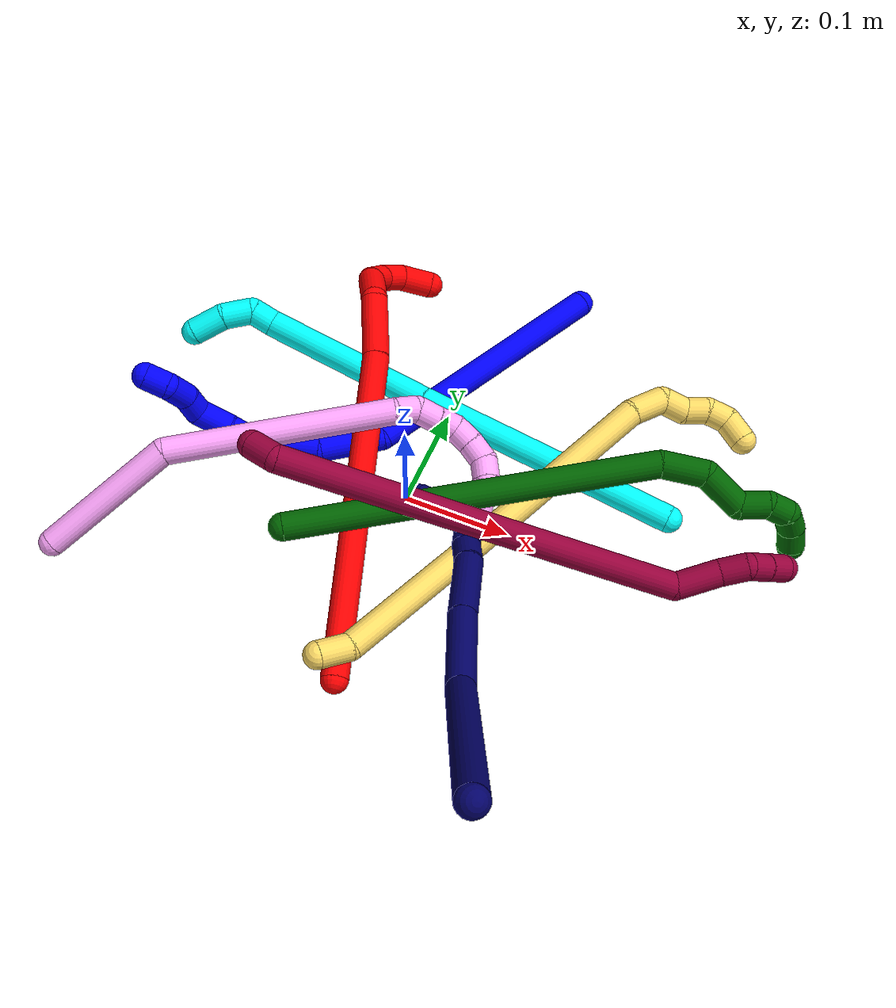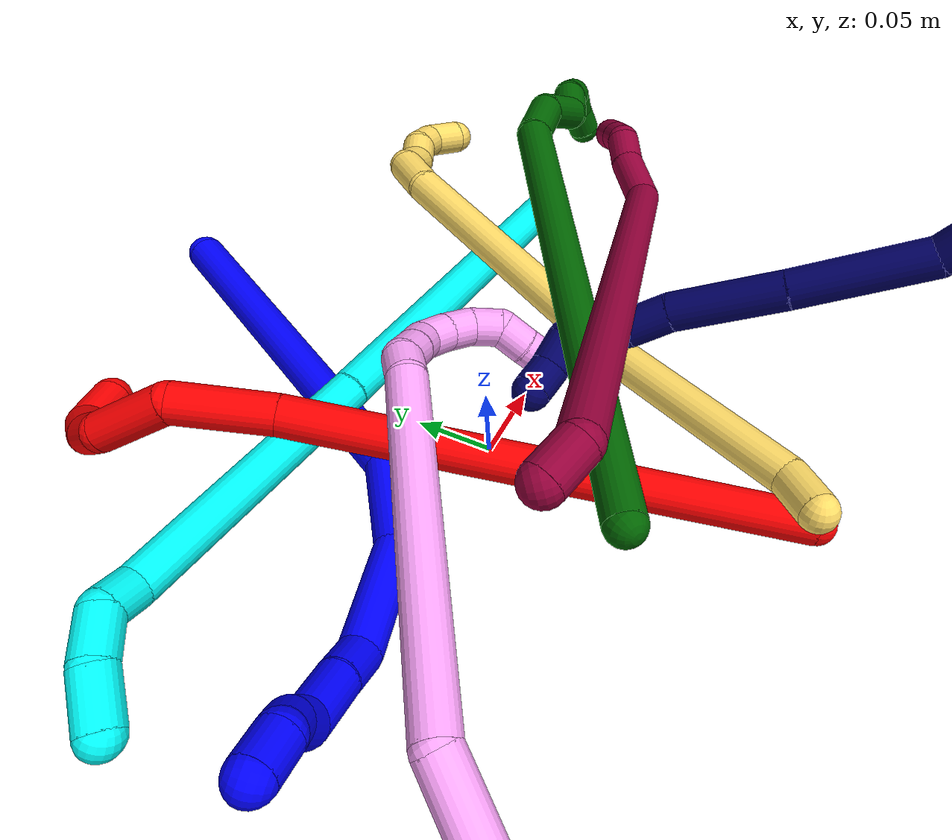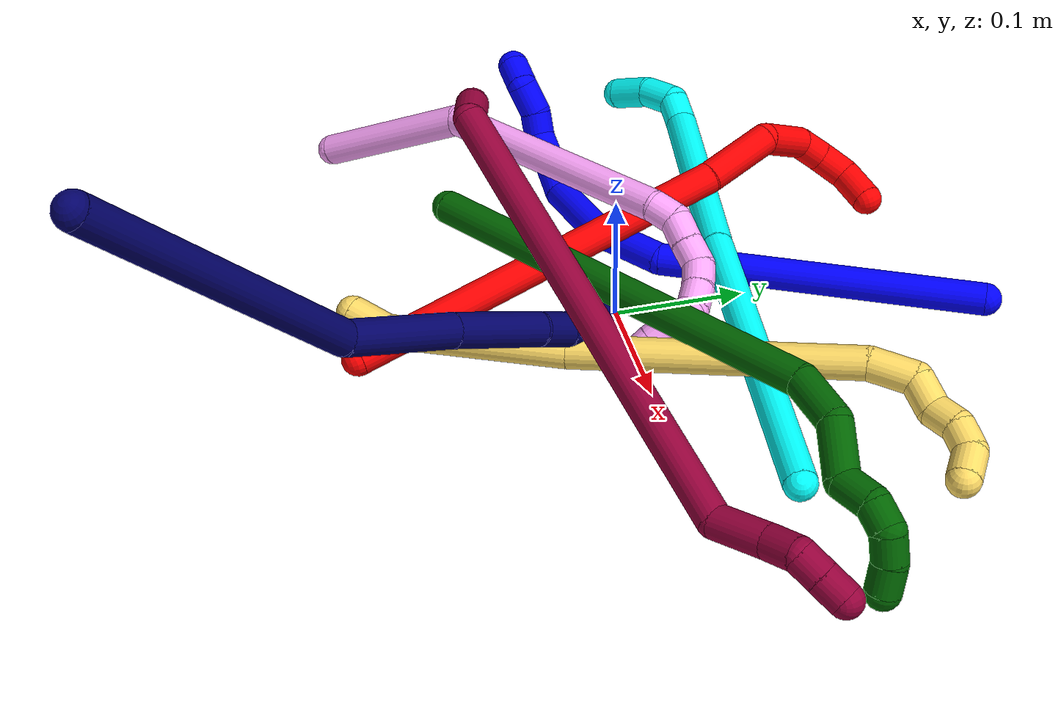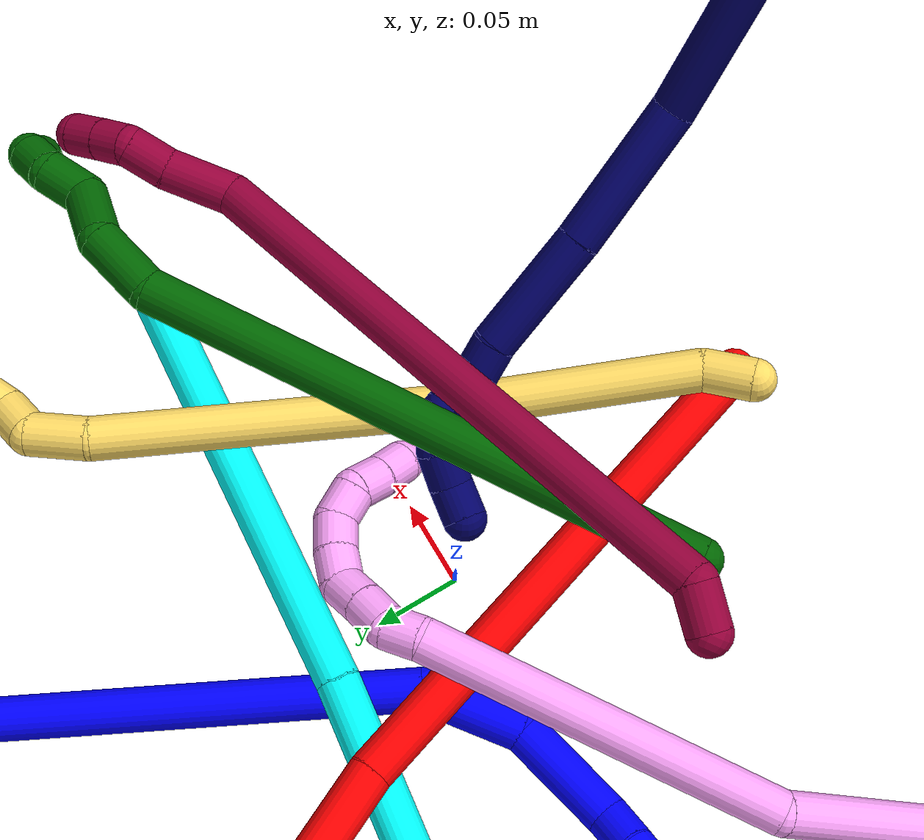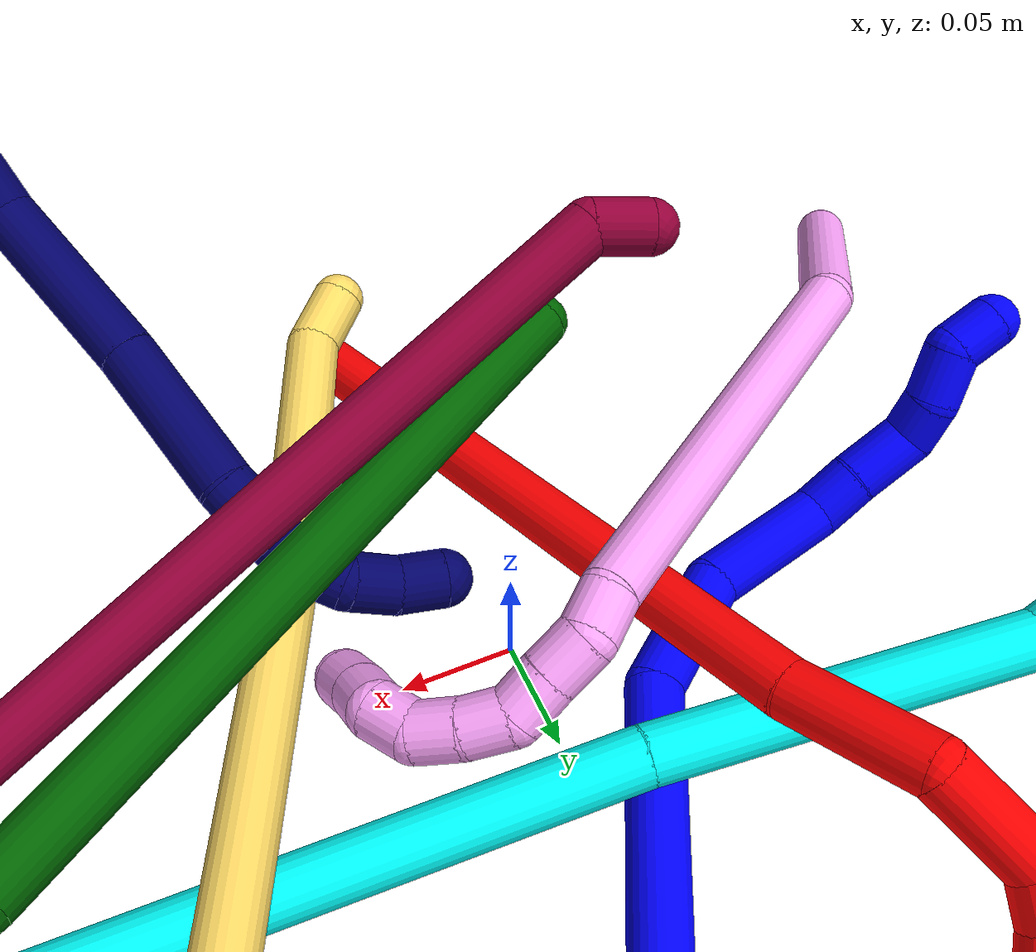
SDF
<sdf version="1.7">
 <world name="default">
  <plugin name="TubeGeneratorPlugin" filename="libtube_generator_plugin.so"/>
  <model name="photoneo_s_sensor">
   <static>1</static>
   <pose>0 0 2 1.57079 1.57079 3.14159</pose>
   <link name="link">
    <inertial><mass>0.1</mass></inertial>
    <sensor name="sensor" type="depth">
     <update_rate>30</update_rate>
     <camera>
      <horizontal_fov>1.22</horizontal_fov>
      <image><width>1920</width><height>1200</height><format>B8G8R8</format></image>
      <clip><near>0.1</near><far>4</far></clip>
      <depth_camera><output>points</output></depth_camera>
     </camera>
     <plugin name="camera_plugin" filename="libgazebo_ros_depth_camera.so">
      <baseline>0.2</baseline>
      <alwaysOn>1</alwaysOn>
      <updateRate>0.0</updateRate>
      <cameraName>camera_ir</cameraName>
      <imageTopicName>/camera/color/image_raw</imageTopicName>
      <cameraInfoTopicName>/camera/color/camera_info</cameraInfoTopicName>
      <depthImageTopicName>/camera/depth/image_raw</depthImageTopicName>
      <depthImageCameraInfoTopicName>/camera/depth/camera_info</depthImageCameraInfoTopicName>
      <pointCloudTopicName>/camera/depth/points</pointCloudTopicName>
      <frameName>fr_optical</frameName>
      <pointCloudCutoff>0.1</pointCloudCutoff>
      <pointCloudCutoffMax>2.0</pointCloudCutoffMax>
      <distortionK1>0</distortionK1>
      <distortionK2>0</distortionK2>
      <distortionK3>0</distortionK3>
      <distortionT1>0</distortionT1>
      <distortionT2>0</distortionT2>
      <CxPrime>0</CxPrime>
      <Cx>0</Cx>
      <Cy>0</Cy>
      <focalLength>0</focalLength>
      <hackBaseline>0</hackBaseline>
     </plugin>
    </sensor>
   </link>
  </model>
  <gravity>0 0 -9.8</gravity>
  <magnetic_field>6e-06 2.3e-05 -4.2e-05</magnetic_field>
  <atmosphere type="adiabatic"/>
  <physics name="default_physics" default="0" type="ode">
   <max_step_size>0.003</max_step_size>
   <real_time_factor>1</real_time_factor>
   <real_time_update_rate>1000</real_time_update_rate>
   <max_contacts>10000</max_contacts>
   <ode>
    <solver>
     <type>quick</type>
     <iters>100</iters>
     <sor>1.3</sor>
     <use_dynamic_moi_rescaling>0</use_dynamic_moi_rescaling>
    </solver>
    <constraints>
     <contact_max_correcting_vel>0</contact_max_correcting_vel>
     <contact_surface_layer>0.001</contact_surface_layer>
     <cfm>0</cfm>
     <erp>0.2</erp>
    </constraints>
   </ode>
  </physics>
  <scene><ambient>0.4 0.4 0.4 1</ambient><background>0.7 0.7 0.7 1</background><shadows>0</shadows></scene>
  <audio><device>default</device></audio>
  <spherical_coordinates>
   <surface_model>EARTH_WGS84</surface_model>
   <latitude_deg>0</latitude_deg>
   <longitude_deg>0</longitude_deg>
   <elevation>0</elevation>
   <heading_deg>0</heading_deg>
  </spherical_coordinates>
  <model name="bin">
   <static>1</static>
   <link name="bottom">
    <collision name="collision-bottom">
     <pose>0 0 -0.01 0 -0 0</pose>
     <geometry><box><size>0.8 0.6 0.02</size></box></geometry>
     <surface>
      <friction><ode><mu>100</mu><mu2>100</mu2></ode></friction>
      <contact><collide_bitmask>65535</collide_bitmask></contact>
     </surface>
    </collision>
   </link>
   <link name="west_wall">
    <collision name="collision-west_wall">
     <pose>-0.41 0 0.1 0 -0 0</pose>
     <geometry><box><size>0.02 0.6 0.2</size></box></geometry>
     <surface>
      <friction><ode><mu>100</mu><mu2>100</mu2></ode></friction>
      <contact><collide_bitmask>65535</collide_bitmask></contact>
     </surface>
    </collision>
   </link>
   <link name="east_wall">
    <collision name="collision-east_wall">
     <pose>0.41 0 0.1 0 -0 0</pose>
     <geometry><box><size>0.02 0.6 0.2</size></box></geometry>
     <surface>
      <friction><ode><mu>100</mu><mu2>100</mu2></ode></friction>
      <contact><collide_bitmask>65535</collide_bitmask></contact>
     </surface>
    </collision>
   </link>
   <link name="south_wall">
    <collision name="collision-south_wall">
     <pose>0 -0.31 0.1 0 -0 0</pose>
     <geometry><box><size>0.8 0.02 0.2</size></box></geometry>
     <surface>
      <friction><ode><mu>100</mu><mu2>100</mu2></ode></friction>
      <contact><collide_bitmask>65535</collide_bitmask></contact>
     </surface>
    </collision>
   </link>
   <link name="north_wall">
    <collision name="collision-north_wall">
     <pose>0 0.31 0.1 0 -0 0</pose>
     <geometry><box><size>0.8 0.02 0.2</size></box></geometry>
     <surface>
      <friction><ode><mu>100</mu><mu2>100</mu2></ode></friction>
      <contact><collide_bitmask>65535</collide_bitmask></contact>
     </surface>
    </collision>
   </link>
  </model>
  <model name="1">
   <static>0</static>
   <link name="1">
    <collision name="collision-cylinder-e_1_1_4">
     <pose>-0.061601 -0.061433 -0.090619 2.54584 -0.512518 -1.41299</pose>
     <geometry><cylinder><radius>0.0125</radius><length>0.25124</length></cylinder></geometry>
     <surface>
      <friction><ode><mu>1.16</mu><mu2>1.16</mu2><slip1>0</slip1><slip2>0</slip2></ode></friction>
      <contact><ode><kp>1e+06</kp><kd>1</kd><max_vel>0</max_vel><min_depth>0.001</min_depth></ode></contact>
     </surface>
    </collision>
    <visual name="visual-cylinder-e_1_1_4">
     <pose>-0.061601 -0.061433 -0.090619 2.54584 -0.512518 -1.41299</pose>
     <geometry><cylinder><radius>0.0125</radius><length>0.25124</length></cylinder></geometry>
     <material><ambient>0 0 1 1</ambient></material>
    </visual>
    <collision name="collision-cylinder-e_2_4_5">
     <pose>-0.146285 -0.138587 -0.192291 2.18357 -0.876533 -1.46827</pose>
     <geometry><cylinder><radius>0.0125</radius><length>0.060073</length></cylinder></geometry>
     <surface>
      <friction><ode><mu>1.16</mu><mu2>1.16</mu2><slip1>0</slip1><slip2>0</slip2></ode></friction>
      <contact><ode><kp>1e+06</kp><kd>1</kd><max_vel>0</max_vel><min_depth>0.001</min_depth></ode></contact>
     </surface>
    </collision>
    <visual name="visual-cylinder-e_2_4_5">
     <pose>-0.146285 -0.138587 -0.192291 2.18357 -0.876533 -1.46827</pose>
     <geometry><cylinder><radius>0.0125</radius><length>0.060073</length></cylinder></geometry>
     <material><ambient>0 0 1 1</ambient></material>
    </visual>
    <collision name="collision-cylinder-e_3_5_6">
     <pose>-0.198591 -0.168714 -0.203225 1.56256 -1.11278 -1.10541</pose>
     <geometry><cylinder><radius>0.0125</radius><length>0.06516</length></cylinder></geometry>
     <surface>
      <friction><ode><mu>1.16</mu><mu2>1.16</mu2><slip1>0</slip1><slip2>0</slip2></ode></friction>
      <contact><ode><kp>1e+06</kp><kd>1</kd><max_vel>0</max_vel><min_depth>0.001</min_depth></ode></contact>
     </surface>
    </collision>
    <visual name="visual-cylinder-e_3_5_6">
     <pose>-0.198591 -0.168714 -0.203225 1.56256 -1.11278 -1.10541</pose>
     <geometry><cylinder><radius>0.0125</radius><length>0.06516</length></cylinder></geometry>
     <material><ambient>0 0 1 1</ambient></material>
    </visual>
    <collision name="collision-cylinder-e_4_6_7">
     <pose>-0.234542 -0.192557 -0.200102 1.26264 -0.596729 -0.442359</pose>
     <geometry><cylinder><radius>0.0125</radius><length>0.023949</length></cylinder></geometry>
     <surface>
      <friction><ode><mu>1.16</mu><mu2>1.16</mu2><slip1>0</slip1><slip2>0</slip2></ode></friction>
      <contact><ode><kp>1e+06</kp><kd>1</kd><max_vel>0</max_vel><min_depth>0.001</min_depth></ode></contact>
     </surface>
    </collision>
    <visual name="visual-cylinder-e_4_6_7">
     <pose>-0.234542 -0.192557 -0.200102 1.26264 -0.596729 -0.442359</pose>
     <geometry><cylinder><radius>0.0125</radius><length>0.023949</length></cylinder></geometry>
     <material><ambient>0 0 1 1</ambient></material>
    </visual>
    <collision name="collision-cylinder-e_5_7_8">
     <pose>-0.251666 -0.213442 -0.193259 1.2472 -0.71083 -0.521846</pose>
     <geometry><cylinder><radius>0.0125</radius><length>0.031864</length></cylinder></geometry>
     <surface>
      <friction><ode><mu>1.16</mu><mu2>1.16</mu2><slip1>0</slip1><slip2>0</slip2></ode></friction>
      <contact><ode><kp>1e+06</kp><kd>1</kd><max_vel>0</max_vel><min_depth>0.001</min_depth></ode></contact>
     </surface>
    </collision>
    <visual name="visual-cylinder-e_5_7_8">
     <pose>-0.251666 -0.213442 -0.193259 1.2472 -0.71083 -0.521846</pose>
     <geometry><cylinder><radius>0.0125</radius><length>0.031864</length></cylinder></geometry>
     <material><ambient>0 0 1 1</ambient></material>
    </visual>
    <collision name="collision-cylinder-e_6_8_9">
     <pose>-0.261903 -0.234998 -0.186156 1.25846 0.014832 0.010797</pose>
     <geometry><cylinder><radius>0.0125</radius><length>0.021247</length></cylinder></geometry>
     <surface>
      <friction><ode><mu>1.16</mu><mu2>1.16</mu2><slip1>0</slip1><slip2>0</slip2></ode></friction>
      <contact><ode><kp>1e+06</kp><kd>1</kd><max_vel>0</max_vel><min_depth>0.001</min_depth></ode></contact>
     </surface>
    </collision>
    <visual name="visual-cylinder-e_6_8_9">
     <pose>-0.261903 -0.234998 -0.186156 1.25846 0.014832 0.010797</pose>
     <geometry><cylinder><radius>0.0125</radius><length>0.021247</length></cylinder></geometry>
     <material><ambient>0 0 1 1</ambient></material>
    </visual>
    <collision name="collision-cylinder-e_7_9_10">
     <pose>-0.262941 -0.257236 -0.182487 1.53744 -0.09818 -0.094963</pose>
     <geometry><cylinder><radius>0.0125</radius><length>0.024391</length></cylinder></geometry>
     <surface>
      <friction><ode><mu>1.16</mu><mu2>1.16</mu2><slip1>0</slip1><slip2>0</slip2></ode></friction>
      <contact><ode><kp>1e+06</kp><kd>1</kd><max_vel>0</max_vel><min_depth>0.001</min_depth></ode></contact>
     </surface>
    </collision>
    <visual name="visual-cylinder-e_7_9_10">
     <pose>-0.262941 -0.257236 -0.182487 1.53744 -0.09818 -0.094963</pose>
     <geometry><cylinder><radius>0.0125</radius><length>0.024391</length></cylinder></geometry>
     <material><ambient>0 0 1 1</ambient></material>
    </visual>
    <collision name="collision-cylinder-e_8_10_2">
     <pose>-0.271958 -0.276797 -0.179749 1.26654 -0.787481 -0.592047</pose>
     <geometry><cylinder><radius>0.0125</radius><length>0.022076</length></cylinder></geometry>
     <surface>
      <friction><ode><mu>1.16</mu><mu2>1.16</mu2><slip1>0</slip1><slip2>0</slip2></ode></friction>
      <contact><ode><kp>1e+06</kp><kd>1</kd><max_vel>0</max_vel><min_depth>0.001</min_depth></ode></contact>
     </surface>
    </collision>
    <visual name="visual-cylinder-e_8_10_2">
     <pose>-0.271958 -0.276797 -0.179749 1.26654 -0.787481 -0.592047</pose>
     <geometry><cylinder><radius>0.0125</radius><length>0.022076</length></cylinder></geometry>
     <material><ambient>0 0 1 1</ambient></material>
    </visual>
    <collision name="collision-sphere-2">
     <pose>-0.279779 -0.284228 -0.177415 0 -0 0</pose>
     <geometry><sphere><radius>0.0125</radius></sphere></geometry>
     <surface>
      <friction><ode><mu>1.16</mu><mu2>1.16</mu2><slip1>0</slip1><slip2>0</slip2></ode></friction>
      <contact><ode><kp>1e+06</kp><kd>1</kd><max_vel>0</max_vel><min_depth>0.001</min_depth></ode></contact>
     </surface>
    </collision>
    <visual name="visual-sphere-2">
     <pose>-0.279779 -0.284228 -0.177415 0 -0 0</pose>
     <geometry><sphere><radius>0.0125</radius></sphere></geometry>
     <material><ambient>0 0 1 1</ambient></material>
    </visual>
    <collision name="collision-sphere-10">
     <pose>-0.264137 -0.269366 -0.182082 0 -0 0</pose>
     <geometry><sphere><radius>0.0125</radius></sphere></geometry>
     <surface>
      <friction><ode><mu>1.16</mu><mu2>1.16</mu2><slip1>0</slip1><slip2>0</slip2></ode></friction>
      <contact><ode><kp>1e+06</kp><kd>1</kd><max_vel>0</max_vel><min_depth>0.001</min_depth></ode></contact>
     </surface>
    </collision>
    <visual name="visual-sphere-10">
     <pose>-0.264137 -0.269366 -0.182082 0 -0 0</pose>
     <geometry><sphere><radius>0.0125</radius></sphere></geometry>
     <material><ambient>0 0 1 1</ambient></material>
    </visual>
    <collision name="collision-sphere-9">
     <pose>-0.261746 -0.245106 -0.182892 0 -0 0</pose>
     <geometry><sphere><radius>0.0125</radius></sphere></geometry>
     <surface>
      <friction><ode><mu>1.16</mu><mu2>1.16</mu2><slip1>0</slip1><slip2>0</slip2></ode></friction>
      <contact><ode><kp>1e+06</kp><kd>1</kd><max_vel>0</max_vel><min_depth>0.001</min_depth></ode></contact>
     </surface>
    </collision>
    <visual name="visual-sphere-9">
     <pose>-0.261746 -0.245106 -0.182892 0 -0 0</pose>
     <geometry><sphere><radius>0.0125</radius></sphere></geometry>
     <material><ambient>0 0 1 1</ambient></material>
    </visual>
    <collision name="collision-sphere-4">
     <pose>-0.123201 -0.122865 -0.181238 0 -0 0</pose>
     <geometry><sphere><radius>0.0125</radius></sphere></geometry>
     <surface>
      <friction><ode><mu>1.16</mu><mu2>1.16</mu2><slip1>0</slip1><slip2>0</slip2></ode></friction>
      <contact><ode><kp>1e+06</kp><kd>1</kd><max_vel>0</max_vel><min_depth>0.001</min_depth></ode></contact>
     </surface>
    </collision>
    <visual name="visual-sphere-4">
     <pose>-0.123201 -0.122865 -0.181238 0 -0 0</pose>
     <geometry><sphere><radius>0.0125</radius></sphere></geometry>
     <material><ambient>0 0 1 1</ambient></material>
    </visual>
    <collision name="collision-sphere-1">
     <geometry><sphere><radius>0.0125</radius></sphere></geometry>
     <surface>
      <friction><ode><mu>1.16</mu><mu2>1.16</mu2><slip1>0</slip1><slip2>0</slip2></ode></friction>
      <contact><ode><kp>1e+06</kp><kd>1</kd><max_vel>0</max_vel><min_depth>0.001</min_depth></ode></contact>
     </surface>
    </collision>
    <visual name="visual-sphere-1">
     <geometry><sphere><radius>0.0125</radius></sphere></geometry>
     <material><ambient>0 0 1 1</ambient></material>
    </visual>
    <collision name="collision-sphere-8">
     <pose>-0.262061 -0.224889 -0.18942 0 -0 0</pose>
     <geometry><sphere><radius>0.0125</radius></sphere></geometry>
     <surface>
      <friction><ode><mu>1.16</mu><mu2>1.16</mu2><slip1>0</slip1><slip2>0</slip2></ode></friction>
      <contact><ode><kp>1e+06</kp><kd>1</kd><max_vel>0</max_vel><min_depth>0.001</min_depth></ode></contact>
     </surface>
    </collision>
    <visual name="visual-sphere-8">
     <pose>-0.262061 -0.224889 -0.18942 0 -0 0</pose>
     <geometry><sphere><radius>0.0125</radius></sphere></geometry>
     <material><ambient>0 0 1 1</ambient></material>
    </visual>
    <collision name="collision-sphere-5">
     <pose>-0.169369 -0.154308 -0.203344 0 -0 0</pose>
     <geometry><sphere><radius>0.0125</radius></sphere></geometry>
     <surface>
      <friction><ode><mu>1.16</mu><mu2>1.16</mu2><slip1>0</slip1><slip2>0</slip2></ode></friction>
      <contact><ode><kp>1e+06</kp><kd>1</kd><max_vel>0</max_vel><min_depth>0.001</min_depth></ode></contact>
     </surface>
    </collision>
    <visual name="visual-sphere-5">
     <pose>-0.169369 -0.154308 -0.203344 0 -0 0</pose>
     <geometry><sphere><radius>0.0125</radius></sphere></geometry>
     <material><ambient>0 0 1 1</ambient></material>
    </visual>
    <collision name="collision-sphere-6">
     <pose>-0.227813 -0.183119 -0.203107 0 -0 0</pose>
     <geometry><sphere><radius>0.0125</radius></sphere></geometry>
     <surface>
      <friction><ode><mu>1.16</mu><mu2>1.16</mu2><slip1>0</slip1><slip2>0</slip2></ode></friction>
      <contact><ode><kp>1e+06</kp><kd>1</kd><max_vel>0</max_vel><min_depth>0.001</min_depth></ode></contact>
     </surface>
    </collision>
    <visual name="visual-sphere-6">
     <pose>-0.227813 -0.183119 -0.203107 0 -0 0</pose>
     <geometry><sphere><radius>0.0125</radius></sphere></geometry>
     <material><ambient>0 0 1 1</ambient></material>
    </visual>
    <collision name="collision-sphere-7">
     <pose>-0.241271 -0.201996 -0.197098 0 -0 0</pose>
     <geometry><sphere><radius>0.0125</radius></sphere></geometry>
     <surface>
      <friction><ode><mu>1.16</mu><mu2>1.16</mu2><slip1>0</slip1><slip2>0</slip2></ode></friction>
      <contact><ode><kp>1e+06</kp><kd>1</kd><max_vel>0</max_vel><min_depth>0.001</min_depth></ode></contact>
     </surface>
    </collision>
    <visual name="visual-sphere-7">
     <pose>-0.241271 -0.201996 -0.197098 0 -0 0</pose>
     <geometry><sphere><radius>0.0125</radius></sphere></geometry>
     <material><ambient>0 0 1 1</ambient></material>
    </visual>
    <inertial>
     <pose>-0.137645 -0.127087 -0.141771 0 -0 0</pose>
     <mass>0.5</mass>
     <inertia>
      <ixx>-0.000996</ixx>
      <ixy>0</ixy>
      <ixz>0</ixz>
      <iyy>-0.000968</iyy>
      <iyz>0</iyz>
      <izz>0.001365</izz>
     </inertia>
    </inertial>
   </link>
   <pose>0.067678 0.27225 0.011498 -1.2482 -0.447068 0.112847</pose>
  </model>
  <model name="2">
   <static>0</static>
   <link name="2">
    <collision name="collision-cylinder-e_1_1_4">
     <pose>-0.007252 -0.004615 0.156243 0.029531 -0.046358 -0.000685</pose>
     <geometry><cylinder><radius>0.0125</radius><length>0.312959</length></cylinder></geometry>
     <surface>
      <friction><ode><mu>1.16</mu><mu2>1.16</mu2><slip1>0</slip1><slip2>0</slip2></ode></friction>
      <contact><ode><kp>1e+06</kp><kd>1</kd><max_vel>0</max_vel><min_depth>0.001</min_depth></ode></contact>
     </surface>
    </collision>
    <visual name="visual-cylinder-e_1_1_4">
     <pose>-0.007252 -0.004615 0.156243 0.029531 -0.046358 -0.000685</pose>
     <geometry><cylinder><radius>0.0125</radius><length>0.312959</length></cylinder></geometry>
     <material><ambient>1 0 0 1</ambient></material>
    </visual>
    <collision name="collision-cylinder-e_2_4_5">
     <pose>-0.019355 -0.012585 0.342227 0.112306 -0.160712 -0.009053</pose>
     <geometry><cylinder><radius>0.0125</radius><length>0.060639</length></cylinder></geometry>
     <surface>
      <friction><ode><mu>1.16</mu><mu2>1.16</mu2><slip1>0</slip1><slip2>0</slip2></ode></friction>
      <contact><ode><kp>1e+06</kp><kd>1</kd><max_vel>0</max_vel><min_depth>0.001</min_depth></ode></contact>
     </surface>
    </collision>
    <visual name="visual-cylinder-e_2_4_5">
     <pose>-0.019355 -0.012585 0.342227 0.112306 -0.160712 -0.009053</pose>
     <geometry><cylinder><radius>0.0125</radius><length>0.060639</length></cylinder></geometry>
     <material><ambient>1 0 0 1</ambient></material>
    </visual>
    <collision name="collision-cylinder-e_3_5_6">
     <pose>-0.034127 -0.004891 0.390769 -0.531255 -0.426937 0.117812</pose>
     <geometry><cylinder><radius>0.0125</radius><length>0.047917</length></cylinder></geometry>
     <surface>
      <friction><ode><mu>1.16</mu><mu2>1.16</mu2><slip1>0</slip1><slip2>0</slip2></ode></friction>
      <contact><ode><kp>1e+06</kp><kd>1</kd><max_vel>0</max_vel><min_depth>0.001</min_depth></ode></contact>
     </surface>
    </collision>
    <visual name="visual-cylinder-e_3_5_6">
     <pose>-0.034127 -0.004891 0.390769 -0.531255 -0.426937 0.117812</pose>
     <geometry><cylinder><radius>0.0125</radius><length>0.047917</length></cylinder></geometry>
     <material><ambient>1 0 0 1</ambient></material>
    </visual>
    <collision name="collision-cylinder-e_4_6_7">
     <pose>-0.043724 0.015041 0.416463 -0.910974 0.02881 -0.014113</pose>
     <geometry><cylinder><radius>0.0125</radius><length>0.022497</length></cylinder></geometry>
     <surface>
      <friction><ode><mu>1.16</mu><mu2>1.16</mu2><slip1>0</slip1><slip2>0</slip2></ode></friction>
      <contact><ode><kp>1e+06</kp><kd>1</kd><max_vel>0</max_vel><min_depth>0.001</min_depth></ode></contact>
     </surface>
    </collision>
    <visual name="visual-cylinder-e_4_6_7">
     <pose>-0.043724 0.015041 0.416463 -0.910974 0.02881 -0.014113</pose>
     <geometry><cylinder><radius>0.0125</radius><length>0.022497</length></cylinder></geometry>
     <material><ambient>1 0 0 1</ambient></material>
    </visual>
    <collision name="collision-cylinder-e_5_7_8">
     <pose>-0.038681 0.03413 0.429854 -1.00374 0.371907 -0.205734</pose>
     <geometry><cylinder><radius>0.0125</radius><length>0.025972</length></cylinder></geometry>
     <surface>
      <friction><ode><mu>1.16</mu><mu2>1.16</mu2><slip1>0</slip1><slip2>0</slip2></ode></friction>
      <contact><ode><kp>1e+06</kp><kd>1</kd><max_vel>0</max_vel><min_depth>0.001</min_depth></ode></contact>
     </surface>
    </collision>
    <visual name="visual-cylinder-e_5_7_8">
     <pose>-0.038681 0.03413 0.429854 -1.00374 0.371907 -0.205734</pose>
     <geometry><cylinder><radius>0.0125</radius><length>0.025972</length></cylinder></geometry>
     <material><ambient>1 0 0 1</ambient></material>
    </visual>
    <collision name="collision-cylinder-e_6_8_2">
     <pose>-0.021917 0.053284 0.436635 -1.53929 0.931532 -0.906481</pose>
     <geometry><cylinder><radius>0.0125</radius><length>0.030016</length></cylinder></geometry>
     <surface>
      <friction><ode><mu>1.16</mu><mu2>1.16</mu2><slip1>0</slip1><slip2>0</slip2></ode></friction>
      <contact><ode><kp>1e+06</kp><kd>1</kd><max_vel>0</max_vel><min_depth>0.001</min_depth></ode></contact>
     </surface>
    </collision>
    <visual name="visual-cylinder-e_6_8_2">
     <pose>-0.021917 0.053284 0.436635 -1.53929 0.931532 -0.906481</pose>
     <geometry><cylinder><radius>0.0125</radius><length>0.030016</length></cylinder></geometry>
     <material><ambient>1 0 0 1</ambient></material>
    </visual>
    <collision name="collision-sphere-2">
     <pose>-0.009873 0.062233 0.436917 0 -0 0</pose>
     <geometry><sphere><radius>0.0125</radius></sphere></geometry>
     <surface>
      <friction><ode><mu>1.16</mu><mu2>1.16</mu2><slip1>0</slip1><slip2>0</slip2></ode></friction>
      <contact><ode><kp>1e+06</kp><kd>1</kd><max_vel>0</max_vel><min_depth>0.001</min_depth></ode></contact>
     </surface>
    </collision>
    <visual name="visual-sphere-2">
     <pose>-0.009873 0.062233 0.436917 0 -0 0</pose>
     <geometry><sphere><radius>0.0125</radius></sphere></geometry>
     <material><ambient>1 0 0 1</ambient></material>
    </visual>
    <collision name="collision-sphere-4">
     <pose>-0.014503 -0.009231 0.312487 0 -0 0</pose>
     <geometry><sphere><radius>0.0125</radius></sphere></geometry>
     <surface>
      <friction><ode><mu>1.16</mu><mu2>1.16</mu2><slip1>0</slip1><slip2>0</slip2></ode></friction>
      <contact><ode><kp>1e+06</kp><kd>1</kd><max_vel>0</max_vel><min_depth>0.001</min_depth></ode></contact>
     </surface>
    </collision>
    <visual name="visual-sphere-4">
     <pose>-0.014503 -0.009231 0.312487 0 -0 0</pose>
     <geometry><sphere><radius>0.0125</radius></sphere></geometry>
     <material><ambient>1 0 0 1</ambient></material>
    </visual>
    <collision name="collision-sphere-1">
     <geometry><sphere><radius>0.0125</radius></sphere></geometry>
     <surface>
      <friction><ode><mu>1.16</mu><mu2>1.16</mu2><slip1>0</slip1><slip2>0</slip2></ode></friction>
      <contact><ode><kp>1e+06</kp><kd>1</kd><max_vel>0</max_vel><min_depth>0.001</min_depth></ode></contact>
     </surface>
    </collision>
    <visual name="visual-sphere-1">
     <geometry><sphere><radius>0.0125</radius></sphere></geometry>
     <material><ambient>1 0 0 1</ambient></material>
    </visual>
    <collision name="collision-sphere-8">
     <pose>-0.033962 0.044334 0.436353 0 -0 0</pose>
     <geometry><sphere><radius>0.0125</radius></sphere></geometry>
     <surface>
      <friction><ode><mu>1.16</mu><mu2>1.16</mu2><slip1>0</slip1><slip2>0</slip2></ode></friction>
      <contact><ode><kp>1e+06</kp><kd>1</kd><max_vel>0</max_vel><min_depth>0.001</min_depth></ode></contact>
     </surface>
    </collision>
    <visual name="visual-sphere-8">
     <pose>-0.033962 0.044334 0.436353 0 -0 0</pose>
     <geometry><sphere><radius>0.0125</radius></sphere></geometry>
     <material><ambient>1 0 0 1</ambient></material>
    </visual>
    <collision name="collision-sphere-5">
     <pose>-0.024207 -0.015939 0.371967 0 -0 0</pose>
     <geometry><sphere><radius>0.0125</radius></sphere></geometry>
     <surface>
      <friction><ode><mu>1.16</mu><mu2>1.16</mu2><slip1>0</slip1><slip2>0</slip2></ode></friction>
      <contact><ode><kp>1e+06</kp><kd>1</kd><max_vel>0</max_vel><min_depth>0.001</min_depth></ode></contact>
     </surface>
    </collision>
    <visual name="visual-sphere-5">
     <pose>-0.024207 -0.015939 0.371967 0 -0 0</pose>
     <geometry><sphere><radius>0.0125</radius></sphere></geometry>
     <material><ambient>1 0 0 1</ambient></material>
    </visual>
    <collision name="collision-sphere-6">
     <pose>-0.044048 0.006157 0.409571 0 -0 0</pose>
     <geometry><sphere><radius>0.0125</radius></sphere></geometry>
     <surface>
      <friction><ode><mu>1.16</mu><mu2>1.16</mu2><slip1>0</slip1><slip2>0</slip2></ode></friction>
      <contact><ode><kp>1e+06</kp><kd>1</kd><max_vel>0</max_vel><min_depth>0.001</min_depth></ode></contact>
     </surface>
    </collision>
    <visual name="visual-sphere-6">
     <pose>-0.044048 0.006157 0.409571 0 -0 0</pose>
     <geometry><sphere><radius>0.0125</radius></sphere></geometry>
     <material><ambient>1 0 0 1</ambient></material>
    </visual>
    <collision name="collision-sphere-7">
     <pose>-0.0434 0.023925 0.423356 0 -0 0</pose>
     <geometry><sphere><radius>0.0125</radius></sphere></geometry>
     <surface>
      <friction><ode><mu>1.16</mu><mu2>1.16</mu2><slip1>0</slip1><slip2>0</slip2></ode></friction>
      <contact><ode><kp>1e+06</kp><kd>1</kd><max_vel>0</max_vel><min_depth>0.001</min_depth></ode></contact>
     </surface>
    </collision>
    <visual name="visual-sphere-7">
     <pose>-0.0434 0.023925 0.423356 0 -0 0</pose>
     <geometry><sphere><radius>0.0125</radius></sphere></geometry>
     <material><ambient>1 0 0 1</ambient></material>
    </visual>
    <inertial>
     <pose>-0.015449 0.000765 0.244028 0 -0 0</pose>
     <mass>0.5</mass>
     <inertia>
      <ixx>0.002596</ixx>
      <ixy>0</ixy>
      <ixz>0</ixz>
      <iyy>0.002603</iyy>
      <iyz>0</iyz>
      <izz>0.000225</izz>
     </inertia>
    </inertial>
   </link>
   <pose>0.022462 -0.199701 0.011494 -1.40688 -0.360816 0.196092</pose>
  </model>
  <model name="3">
   <static>0</static>
   <link name="3">
    <collision name="collision-cylinder-e_1_1_4">
     <pose>-0.109169 0.001915 -0.061105 -3.11026 -1.0603 3.08814</pose>
     <geometry><cylinder><radius>0.0125</radius><length>0.250242</length></cylinder></geometry>
     <surface>
      <friction><ode><mu>1.16</mu><mu2>1.16</mu2><slip1>0</slip1><slip2>0</slip2></ode></friction>
      <contact><ode><kp>1e+06</kp><kd>1</kd><max_vel>0</max_vel><min_depth>0.001</min_depth></ode></contact>
     </surface>
    </collision>
    <visual name="visual-cylinder-e_1_1_4">
     <pose>-0.109169 0.001915 -0.061105 -3.11026 -1.0603 3.08814</pose>
     <geometry><cylinder><radius>0.0125</radius><length>0.250242</length></cylinder></geometry>
     <material><ambient>0.003922 1 0.996078 1</ambient></material>
    </visual>
    <collision name="collision-cylinder-e_2_4_5">
     <pose>-0.289275 0.008742 -0.16645 -3.03104 -1.01041 2.94216</pose>
     <geometry><cylinder><radius>0.0125</radius><length>0.167492</length></cylinder></geometry>
     <surface>
      <friction><ode><mu>1.16</mu><mu2>1.16</mu2><slip1>0</slip1><slip2>0</slip2></ode></friction>
      <contact><ode><kp>1e+06</kp><kd>1</kd><max_vel>0</max_vel><min_depth>0.001</min_depth></ode></contact>
     </surface>
    </collision>
    <visual name="visual-cylinder-e_2_4_5">
     <pose>-0.289275 0.008742 -0.16645 -3.03104 -1.01041 2.94216</pose>
     <geometry><cylinder><radius>0.0125</radius><length>0.167492</length></cylinder></geometry>
     <material><ambient>0.003922 1 0.996078 1</ambient></material>
    </visual>
    <collision name="collision-cylinder-e_3_5_6">
     <pose>-0.371616 0.012823 -0.212126 2.61772 -1.4264 -2.54056</pose>
     <geometry><cylinder><radius>0.0125</radius><length>0.023048</length></cylinder></geometry>
     <surface>
      <friction><ode><mu>1.16</mu><mu2>1.16</mu2><slip1>0</slip1><slip2>0</slip2></ode></friction>
      <contact><ode><kp>1e+06</kp><kd>1</kd><max_vel>0</max_vel><min_depth>0.001</min_depth></ode></contact>
     </surface>
    </collision>
    <visual name="visual-cylinder-e_3_5_6">
     <pose>-0.371616 0.012823 -0.212126 2.61772 -1.4264 -2.54056</pose>
     <geometry><cylinder><radius>0.0125</radius><length>0.023048</length></cylinder></geometry>
     <material><ambient>0.003922 1 0.996078 1</ambient></material>
    </visual>
    <collision name="collision-cylinder-e_4_6_7">
     <pose>-0.391951 0.003469 -0.220019 2.21903 -0.695765 -1.2606</pose>
     <geometry><cylinder><radius>0.0125</radius><length>0.027866</length></cylinder></geometry>
     <surface>
      <friction><ode><mu>1.16</mu><mu2>1.16</mu2><slip1>0</slip1><slip2>0</slip2></ode></friction>
      <contact><ode><kp>1e+06</kp><kd>1</kd><max_vel>0</max_vel><min_depth>0.001</min_depth></ode></contact>
     </surface>
    </collision>
    <visual name="visual-cylinder-e_4_6_7">
     <pose>-0.391951 0.003469 -0.220019 2.21903 -0.695765 -1.2606</pose>
     <geometry><cylinder><radius>0.0125</radius><length>0.027866</length></cylinder></geometry>
     <material><ambient>0.003922 1 0.996078 1</ambient></material>
    </visual>
    <collision name="collision-cylinder-e_5_7_2">
     <pose>-0.406836 -0.016279 -0.23566 2.25662 -0.389629 -0.789191</pose>
     <geometry><cylinder><radius>0.0125</radius><length>0.031352</length></cylinder></geometry>
     <surface>
      <friction><ode><mu>1.16</mu><mu2>1.16</mu2><slip1>0</slip1><slip2>0</slip2></ode></friction>
      <contact><ode><kp>1e+06</kp><kd>1</kd><max_vel>0</max_vel><min_depth>0.001</min_depth></ode></contact>
     </surface>
    </collision>
    <visual name="visual-cylinder-e_5_7_2">
     <pose>-0.406836 -0.016279 -0.23566 2.25662 -0.389629 -0.789191</pose>
     <geometry><cylinder><radius>0.0125</radius><length>0.031352</length></cylinder></geometry>
     <material><ambient>0.003922 1 0.996078 1</ambient></material>
    </visual>
    <collision name="collision-sphere-2">
     <pose>-0.41279 -0.027501 -0.244844 0 -0 0</pose>
     <geometry><sphere><radius>0.0125</radius></sphere></geometry>
     <surface>
      <friction><ode><mu>1.16</mu><mu2>1.16</mu2><slip1>0</slip1><slip2>0</slip2></ode></friction>
      <contact><ode><kp>1e+06</kp><kd>1</kd><max_vel>0</max_vel><min_depth>0.001</min_depth></ode></contact>
     </surface>
    </collision>
    <visual name="visual-sphere-2">
     <pose>-0.41279 -0.027501 -0.244844 0 -0 0</pose>
     <geometry><sphere><radius>0.0125</radius></sphere></geometry>
     <material><ambient>0.003922 1 0.996078 1</ambient></material>
    </visual>
    <collision name="collision-sphere-7">
     <pose>-0.400881 -0.005056 -0.226476 0 -0 0</pose>
     <geometry><sphere><radius>0.0125</radius></sphere></geometry>
     <surface>
      <friction><ode><mu>1.16</mu><mu2>1.16</mu2><slip1>0</slip1><slip2>0</slip2></ode></friction>
      <contact><ode><kp>1e+06</kp><kd>1</kd><max_vel>0</max_vel><min_depth>0.001</min_depth></ode></contact>
     </surface>
    </collision>
    <visual name="visual-sphere-7">
     <pose>-0.400881 -0.005056 -0.226476 0 -0 0</pose>
     <geometry><sphere><radius>0.0125</radius></sphere></geometry>
     <material><ambient>0.003922 1 0.996078 1</ambient></material>
    </visual>
    <collision name="collision-sphere-6">
     <pose>-0.38302 0.011994 -0.213562 0 -0 0</pose>
     <geometry><sphere><radius>0.0125</radius></sphere></geometry>
     <surface>
      <friction><ode><mu>1.16</mu><mu2>1.16</mu2><slip1>0</slip1><slip2>0</slip2></ode></friction>
      <contact><ode><kp>1e+06</kp><kd>1</kd><max_vel>0</max_vel><min_depth>0.001</min_depth></ode></contact>
     </surface>
    </collision>
    <visual name="visual-sphere-6">
     <pose>-0.38302 0.011994 -0.213562 0 -0 0</pose>
     <geometry><sphere><radius>0.0125</radius></sphere></geometry>
     <material><ambient>0.003922 1 0.996078 1</ambient></material>
    </visual>
    <collision name="collision-sphere-5">
     <pose>-0.360212 0.013653 -0.210691 0 -0 0</pose>
     <geometry><sphere><radius>0.0125</radius></sphere></geometry>
     <surface>
      <friction><ode><mu>1.16</mu><mu2>1.16</mu2><slip1>0</slip1><slip2>0</slip2></ode></friction>
      <contact><ode><kp>1e+06</kp><kd>1</kd><max_vel>0</max_vel><min_depth>0.001</min_depth></ode></contact>
     </surface>
    </collision>
    <visual name="visual-sphere-5">
     <pose>-0.360212 0.013653 -0.210691 0 -0 0</pose>
     <geometry><sphere><radius>0.0125</radius></sphere></geometry>
     <material><ambient>0.003922 1 0.996078 1</ambient></material>
    </visual>
    <collision name="collision-sphere-1">
     <geometry><sphere><radius>0.0125</radius></sphere></geometry>
     <surface>
      <friction><ode><mu>1.16</mu><mu2>1.16</mu2><slip1>0</slip1><slip2>0</slip2></ode></friction>
      <contact><ode><kp>1e+06</kp><kd>1</kd><max_vel>0</max_vel><min_depth>0.001</min_depth></ode></contact>
     </surface>
    </collision>
    <visual name="visual-sphere-1">
     <geometry><sphere><radius>0.0125</radius></sphere></geometry>
     <material><ambient>0.003922 1 0.996078 1</ambient></material>
    </visual>
    <collision name="collision-sphere-4">
     <pose>-0.218337 0.003831 -0.12221 0 -0 0</pose>
     <geometry><sphere><radius>0.0125</radius></sphere></geometry>
     <surface>
      <friction><ode><mu>1.16</mu><mu2>1.16</mu2><slip1>0</slip1><slip2>0</slip2></ode></friction>
      <contact><ode><kp>1e+06</kp><kd>1</kd><max_vel>0</max_vel><min_depth>0.001</min_depth></ode></contact>
     </surface>
    </collision>
    <visual name="visual-sphere-4">
     <pose>-0.218337 0.003831 -0.12221 0 -0 0</pose>
     <geometry><sphere><radius>0.0125</radius></sphere></geometry>
     <material><ambient>0.003922 1 0.996078 1</ambient></material>
    </visual>
    <inertial>
     <pose>-0.216024 0.003651 -0.123157 0 -0 0</pose>
     <mass>0.5</mass>
     <inertia>
      <ixx>-0.000807</ixx>
      <ixy>0</ixy>
      <ixz>0</ixz>
      <iyy>0.001781</iyy>
      <iyz>0</iyz>
      <izz>0.001432</izz>
     </inertia>
    </inertial>
   </link>
   <pose>0.229785 0.067029 0.011979 0.136751 0.597538 0.008771</pose>
  </model>
  <model name="4">
   <static>0</static>
   <link name="4">
    <collision name="collision-cylinder-e_1_1_4">
     <pose>0.009525 0.020167 -0.061052 -2.82256 0.147066 -0.85877</pose>
     <geometry><cylinder><radius>0.0125</radius><length>0.129997</length></cylinder></geometry>
     <surface>
      <friction><ode><mu>1.16</mu><mu2>1.16</mu2><slip1>0</slip1><slip2>0</slip2></ode></friction>
      <contact><ode><kp>1e+06</kp><kd>1</kd><max_vel>0</max_vel><min_depth>0.001</min_depth></ode></contact>
     </surface>
    </collision>
    <visual name="visual-cylinder-e_1_1_4">
     <pose>0.009525 0.020167 -0.061052 -2.82256 0.147066 -0.85877</pose>
     <geometry><cylinder><radius>0.0125</radius><length>0.129997</length></cylinder></geometry>
     <material><ambient>1 0.65098 0.996078 1</ambient></material>
    </visual>
    <collision name="collision-cylinder-e_2_4_5">
     <pose>0.043114 0.019352 -0.221646 2.93385 0.232285 1.68312</pose>
     <geometry><cylinder><radius>0.0125</radius><length>0.209072</length></cylinder></geometry>
     <surface>
      <friction><ode><mu>1.16</mu><mu2>1.16</mu2><slip1>0</slip1><slip2>0</slip2></ode></friction>
      <contact><ode><kp>1e+06</kp><kd>1</kd><max_vel>0</max_vel><min_depth>0.001</min_depth></ode></contact>
     </surface>
    </collision>
    <visual name="visual-cylinder-e_2_4_5">
     <pose>0.043114 0.019352 -0.221646 2.93385 0.232285 1.68312</pose>
     <geometry><cylinder><radius>0.0125</radius><length>0.209072</length></cylinder></geometry>
     <material><ambient>1 0.65098 0.996078 1</ambient></material>
    </visual>
    <collision name="collision-cylinder-e_3_5_6">
     <pose>0.067289 -0.005288 -0.330681 2.77383 0.010939 0.058798</pose>
     <geometry><cylinder><radius>0.0125</radius><length>0.02035</length></cylinder></geometry>
     <surface>
      <friction><ode><mu>1.16</mu><mu2>1.16</mu2><slip1>0</slip1><slip2>0</slip2></ode></friction>
      <contact><ode><kp>1e+06</kp><kd>1</kd><max_vel>0</max_vel><min_depth>0.001</min_depth></ode></contact>
     </surface>
    </collision>
    <visual name="visual-cylinder-e_3_5_6">
     <pose>0.067289 -0.005288 -0.330681 2.77383 0.010939 0.058798</pose>
     <geometry><cylinder><radius>0.0125</radius><length>0.02035</length></cylinder></geometry>
     <material><ambient>1 0.65098 0.996078 1</ambient></material>
    </visual>
    <collision name="collision-cylinder-e_4_6_7">
     <pose>0.069005 -0.016779 -0.346638 2.26064 0.156714 0.330121</pose>
     <geometry><cylinder><radius>0.0125</radius><length>0.020561</length></cylinder></geometry>
     <surface>
      <friction><ode><mu>1.16</mu><mu2>1.16</mu2><slip1>0</slip1><slip2>0</slip2></ode></friction>
      <contact><ode><kp>1e+06</kp><kd>1</kd><max_vel>0</max_vel><min_depth>0.001</min_depth></ode></contact>
     </surface>
    </collision>
    <visual name="visual-cylinder-e_4_6_7">
     <pose>0.069005 -0.016779 -0.346638 2.26064 0.156714 0.330121</pose>
     <geometry><cylinder><radius>0.0125</radius><length>0.020561</length></cylinder></geometry>
     <material><ambient>1 0.65098 0.996078 1</ambient></material>
    </visual>
    <collision name="collision-cylinder-e_5_7_8">
     <pose>0.071651 -0.03213 -0.359625 2.28556 0.10425 0.227724</pose>
     <geometry><cylinder><radius>0.0125</radius><length>0.02002</length></cylinder></geometry>
     <surface>
      <friction><ode><mu>1.16</mu><mu2>1.16</mu2><slip1>0</slip1><slip2>0</slip2></ode></friction>
      <contact><ode><kp>1e+06</kp><kd>1</kd><max_vel>0</max_vel><min_depth>0.001</min_depth></ode></contact>
     </surface>
    </collision>
    <visual name="visual-cylinder-e_5_7_8">
     <pose>0.071651 -0.03213 -0.359625 2.28556 0.10425 0.227724</pose>
     <geometry><cylinder><radius>0.0125</radius><length>0.02002</length></cylinder></geometry>
     <material><ambient>1 0.65098 0.996078 1</ambient></material>
    </visual>
    <collision name="collision-cylinder-e_6_8_9">
     <pose>0.078229 -0.047421 -0.369143 1.93835 0.586639 0.828921</pose>
     <geometry><cylinder><radius>0.0125</radius><length>0.02</length></cylinder></geometry>
     <surface>
      <friction><ode><mu>1.16</mu><mu2>1.16</mu2><slip1>0</slip1><slip2>0</slip2></ode></friction>
      <contact><ode><kp>1e+06</kp><kd>1</kd><max_vel>0</max_vel><min_depth>0.001</min_depth></ode></contact>
     </surface>
    </collision>
    <visual name="visual-cylinder-e_6_8_9">
     <pose>0.078229 -0.047421 -0.369143 1.93835 0.586639 0.828921</pose>
     <geometry><cylinder><radius>0.0125</radius><length>0.02</length></cylinder></geometry>
     <material><ambient>1 0.65098 0.996078 1</ambient></material>
    </visual>
    <collision name="collision-cylinder-e_7_9_10">
     <pose>0.089919 -0.062953 -0.373513 1.74643 0.662939 0.779262</pose>
     <geometry><cylinder><radius>0.0125</radius><length>0.02</length></cylinder></geometry>
     <surface>
      <friction><ode><mu>1.16</mu><mu2>1.16</mu2><slip1>0</slip1><slip2>0</slip2></ode></friction>
      <contact><ode><kp>1e+06</kp><kd>1</kd><max_vel>0</max_vel><min_depth>0.001</min_depth></ode></contact>
     </surface>
    </collision>
    <visual name="visual-cylinder-e_7_9_10">
     <pose>0.089919 -0.062953 -0.373513 1.74643 0.662939 0.779262</pose>
     <geometry><cylinder><radius>0.0125</radius><length>0.02</length></cylinder></geometry>
     <material><ambient>1 0.65098 0.996078 1</ambient></material>
    </visual>
    <collision name="collision-cylinder-e_8_10_11">
     <pose>0.103141 -0.076712 -0.371138 1.01184 0.784898 0.450839</pose>
     <geometry><cylinder><radius>0.0125</radius><length>0.02</length></cylinder></geometry>
     <surface>
      <friction><ode><mu>1.16</mu><mu2>1.16</mu2><slip1>0</slip1><slip2>0</slip2></ode></friction>
      <contact><ode><kp>1e+06</kp><kd>1</kd><max_vel>0</max_vel><min_depth>0.001</min_depth></ode></contact>
     </surface>
    </collision>
    <visual name="visual-cylinder-e_8_10_11">
     <pose>0.103141 -0.076712 -0.371138 1.01184 0.784898 0.450839</pose>
     <geometry><cylinder><radius>0.0125</radius><length>0.02</length></cylinder></geometry>
     <material><ambient>1 0.65098 0.996078 1</ambient></material>
    </visual>
    <collision name="collision-cylinder-e_9_11_12">
     <pose>0.112099 -0.089999 -0.360807 0.83656 0.190206 0.084754</pose>
     <geometry><cylinder><radius>0.0125</radius><length>0.02</length></cylinder></geometry>
     <surface>
      <friction><ode><mu>1.16</mu><mu2>1.16</mu2><slip1>0</slip1><slip2>0</slip2></ode></friction>
      <contact><ode><kp>1e+06</kp><kd>1</kd><max_vel>0</max_vel><min_depth>0.001</min_depth></ode></contact>
     </surface>
    </collision>
    <visual name="visual-cylinder-e_9_11_12">
     <pose>0.112099 -0.089999 -0.360807 0.83656 0.190206 0.084754</pose>
     <geometry><cylinder><radius>0.0125</radius><length>0.02</length></cylinder></geometry>
     <material><ambient>1 0.65098 0.996078 1</ambient></material>
    </visual>
    <collision name="collision-cylinder-e_10_12_2">
     <pose>0.116202 -0.105046 -0.348317 0.919658 0.223147 0.110858</pose>
     <geometry><cylinder><radius>0.0125</radius><length>0.02</length></cylinder></geometry>
     <surface>
      <friction><ode><mu>1.16</mu><mu2>1.16</mu2><slip1>0</slip1><slip2>0</slip2></ode></friction>
      <contact><ode><kp>1e+06</kp><kd>1</kd><max_vel>0</max_vel><min_depth>0.001</min_depth></ode></contact>
     </surface>
    </collision>
    <visual name="visual-cylinder-e_10_12_2">
     <pose>0.116202 -0.105046 -0.348317 0.919658 0.223147 0.110858</pose>
     <geometry><cylinder><radius>0.0125</radius><length>0.02</length></cylinder></geometry>
     <material><ambient>1 0.65098 0.996078 1</ambient></material>
    </visual>
    <collision name="collision-sphere-2">
     <pose>0.118415 -0.112802 -0.342407 0 -0 0</pose>
     <geometry><sphere><radius>0.0125</radius></sphere></geometry>
     <surface>
      <friction><ode><mu>1.16</mu><mu2>1.16</mu2><slip1>0</slip1><slip2>0</slip2></ode></friction>
      <contact><ode><kp>1e+06</kp><kd>1</kd><max_vel>0</max_vel><min_depth>0.001</min_depth></ode></contact>
     </surface>
    </collision>
    <visual name="visual-sphere-2">
     <pose>0.118415 -0.112802 -0.342407 0 -0 0</pose>
     <geometry><sphere><radius>0.0125</radius></sphere></geometry>
     <material><ambient>1 0.65098 0.996078 1</ambient></material>
    </visual>
    <collision name="collision-sphere-12">
     <pose>0.113989 -0.097289 -0.354228 0 -0 0</pose>
     <geometry><sphere><radius>0.0125</radius></sphere></geometry>
     <surface>
      <friction><ode><mu>1.16</mu><mu2>1.16</mu2><slip1>0</slip1><slip2>0</slip2></ode></friction>
      <contact><ode><kp>1e+06</kp><kd>1</kd><max_vel>0</max_vel><min_depth>0.001</min_depth></ode></contact>
     </surface>
    </collision>
    <visual name="visual-sphere-12">
     <pose>0.113989 -0.097289 -0.354228 0 -0 0</pose>
     <geometry><sphere><radius>0.0125</radius></sphere></geometry>
     <material><ambient>1 0.65098 0.996078 1</ambient></material>
    </visual>
    <collision name="collision-sphere-11">
     <pose>0.110208 -0.08271 -0.367387 0 -0 0</pose>
     <geometry><sphere><radius>0.0125</radius></sphere></geometry>
     <surface>
      <friction><ode><mu>1.16</mu><mu2>1.16</mu2><slip1>0</slip1><slip2>0</slip2></ode></friction>
      <contact><ode><kp>1e+06</kp><kd>1</kd><max_vel>0</max_vel><min_depth>0.001</min_depth></ode></contact>
     </surface>
    </collision>
    <visual name="visual-sphere-11">
     <pose>0.110208 -0.08271 -0.367387 0 -0 0</pose>
     <geometry><sphere><radius>0.0125</radius></sphere></geometry>
     <material><ambient>1 0.65098 0.996078 1</ambient></material>
    </visual>
    <collision name="collision-sphere-10">
     <pose>0.096073 -0.070714 -0.37489 0 -0 0</pose>
     <geometry><sphere><radius>0.0125</radius></sphere></geometry>
     <surface>
      <friction><ode><mu>1.16</mu><mu2>1.16</mu2><slip1>0</slip1><slip2>0</slip2></ode></friction>
      <contact><ode><kp>1e+06</kp><kd>1</kd><max_vel>0</max_vel><min_depth>0.001</min_depth></ode></contact>
     </surface>
    </collision>
    <visual name="visual-sphere-10">
     <pose>0.096073 -0.070714 -0.37489 0 -0 0</pose>
     <geometry><sphere><radius>0.0125</radius></sphere></geometry>
     <material><ambient>1 0.65098 0.996078 1</ambient></material>
    </visual>
    <collision name="collision-sphere-9">
     <pose>0.083764 -0.055193 -0.372136 0 -0 0</pose>
     <geometry><sphere><radius>0.0125</radius></sphere></geometry>
     <surface>
      <friction><ode><mu>1.16</mu><mu2>1.16</mu2><slip1>0</slip1><slip2>0</slip2></ode></friction>
      <contact><ode><kp>1e+06</kp><kd>1</kd><max_vel>0</max_vel><min_depth>0.001</min_depth></ode></contact>
     </surface>
    </collision>
    <visual name="visual-sphere-9">
     <pose>0.083764 -0.055193 -0.372136 0 -0 0</pose>
     <geometry><sphere><radius>0.0125</radius></sphere></geometry>
     <material><ambient>1 0.65098 0.996078 1</ambient></material>
    </visual>
    <collision name="collision-sphere-4">
     <pose>0.019049 0.040334 -0.122105 0 -0 0</pose>
     <geometry><sphere><radius>0.0125</radius></sphere></geometry>
     <surface>
      <friction><ode><mu>1.16</mu><mu2>1.16</mu2><slip1>0</slip1><slip2>0</slip2></ode></friction>
      <contact><ode><kp>1e+06</kp><kd>1</kd><max_vel>0</max_vel><min_depth>0.001</min_depth></ode></contact>
     </surface>
    </collision>
    <visual name="visual-sphere-4">
     <pose>0.019049 0.040334 -0.122105 0 -0 0</pose>
     <geometry><sphere><radius>0.0125</radius></sphere></geometry>
     <material><ambient>1 0.65098 0.996078 1</ambient></material>
    </visual>
    <collision name="collision-sphere-1">
     <geometry><sphere><radius>0.0125</radius></sphere></geometry>
     <surface>
      <friction><ode><mu>1.16</mu><mu2>1.16</mu2><slip1>0</slip1><slip2>0</slip2></ode></friction>
      <contact><ode><kp>1e+06</kp><kd>1</kd><max_vel>0</max_vel><min_depth>0.001</min_depth></ode></contact>
     </surface>
    </collision>
    <visual name="visual-sphere-1">
     <geometry><sphere><radius>0.0125</radius></sphere></geometry>
     <material><ambient>1 0.65098 0.996078 1</ambient></material>
    </visual>
    <collision name="collision-sphere-8">
     <pose>0.072693 -0.039649 -0.366151 0 -0 0</pose>
     <geometry><sphere><radius>0.0125</radius></sphere></geometry>
     <surface>
      <friction><ode><mu>1.16</mu><mu2>1.16</mu2><slip1>0</slip1><slip2>0</slip2></ode></friction>
      <contact><ode><kp>1e+06</kp><kd>1</kd><max_vel>0</max_vel><min_depth>0.001</min_depth></ode></contact>
     </surface>
    </collision>
    <visual name="visual-sphere-8">
     <pose>0.072693 -0.039649 -0.366151 0 -0 0</pose>
     <geometry><sphere><radius>0.0125</radius></sphere></geometry>
     <material><ambient>1 0.65098 0.996078 1</ambient></material>
    </visual>
    <collision name="collision-sphere-5">
     <pose>0.067178 -0.00163 -0.321187 0 -0 0</pose>
     <geometry><sphere><radius>0.0125</radius></sphere></geometry>
     <surface>
      <friction><ode><mu>1.16</mu><mu2>1.16</mu2><slip1>0</slip1><slip2>0</slip2></ode></friction>
      <contact><ode><kp>1e+06</kp><kd>1</kd><max_vel>0</max_vel><min_depth>0.001</min_depth></ode></contact>
     </surface>
    </collision>
    <visual name="visual-sphere-5">
     <pose>0.067178 -0.00163 -0.321187 0 -0 0</pose>
     <geometry><sphere><radius>0.0125</radius></sphere></geometry>
     <material><ambient>1 0.65098 0.996078 1</ambient></material>
    </visual>
    <collision name="collision-sphere-6">
     <pose>0.067401 -0.008946 -0.340175 0 -0 0</pose>
     <geometry><sphere><radius>0.0125</radius></sphere></geometry>
     <surface>
      <friction><ode><mu>1.16</mu><mu2>1.16</mu2><slip1>0</slip1><slip2>0</slip2></ode></friction>
      <contact><ode><kp>1e+06</kp><kd>1</kd><max_vel>0</max_vel><min_depth>0.001</min_depth></ode></contact>
     </surface>
    </collision>
    <visual name="visual-sphere-6">
     <pose>0.067401 -0.008946 -0.340175 0 -0 0</pose>
     <geometry><sphere><radius>0.0125</radius></sphere></geometry>
     <material><ambient>1 0.65098 0.996078 1</ambient></material>
    </visual>
    <collision name="collision-sphere-7">
     <pose>0.07061 -0.024611 -0.3531 0 -0 0</pose>
     <geometry><sphere><radius>0.0125</radius></sphere></geometry>
     <surface>
      <friction><ode><mu>1.16</mu><mu2>1.16</mu2><slip1>0</slip1><slip2>0</slip2></ode></friction>
      <contact><ode><kp>1e+06</kp><kd>1</kd><max_vel>0</max_vel><min_depth>0.001</min_depth></ode></contact>
     </surface>
    </collision>
    <visual name="visual-sphere-7">
     <pose>0.07061 -0.024611 -0.3531 0 -0 0</pose>
     <geometry><sphere><radius>0.0125</radius></sphere></geometry>
     <material><ambient>1 0.65098 0.996078 1</ambient></material>
    </visual>
    <inertial>
     <pose>0.048933 -0.004142 -0.223582 0 -0 0</pose>
     <mass>0.5</mass>
     <inertia>
      <ixx>0.000663</ixx>
      <ixy>0</ixy>
      <ixz>0</ixz>
      <iyy>0.000609</iyy>
      <iyz>0</iyz>
      <izz>-0.000131</izz>
     </inertia>
    </inertial>
   </link>
   <pose>-0.266964 -0.176886 0.011912 1.67491 -0.580191 -0.727052</pose>
  </model>
  <model name="5">
   <static>0</static>
   <link name="5">
    <collision name="collision-cylinder-e_1_1_4">
     <pose>0.000305 0.014765 0.00164 -1.4602 0.020551 -0.018395</pose>
     <geometry><cylinder><radius>0.0125</radius><length>0.029718</length></cylinder></geometry>
     <surface>
      <friction><ode><mu>1.16</mu><mu2>1.16</mu2><slip1>0</slip1><slip2>0</slip2></ode></friction>
      <contact><ode><kp>1e+06</kp><kd>1</kd><max_vel>0</max_vel><min_depth>0.001</min_depth></ode></contact>
     </surface>
    </collision>
    <visual name="visual-cylinder-e_1_1_4">
     <pose>0.000305 0.014765 0.00164 -1.4602 0.020551 -0.018395</pose>
     <geometry><cylinder><radius>0.0125</radius><length>0.029718</length></cylinder></geometry>
     <material><ambient>1 0.858824 0.4 1</ambient></material>
    </visual>
    <collision name="collision-cylinder-e_2_4_5">
     <pose>0.027735 0.089232 0.004977 -1.54237 0.426296 -0.414692</pose>
     <geometry><cylinder><radius>0.0125</radius><length>0.131193</length></cylinder></geometry>
     <surface>
      <friction><ode><mu>1.16</mu><mu2>1.16</mu2><slip1>0</slip1><slip2>0</slip2></ode></friction>
      <contact><ode><kp>1e+06</kp><kd>1</kd><max_vel>0</max_vel><min_depth>0.001</min_depth></ode></contact>
     </surface>
    </collision>
    <visual name="visual-cylinder-e_2_4_5">
     <pose>0.027735 0.089232 0.004977 -1.54237 0.426296 -0.414692</pose>
     <geometry><cylinder><radius>0.0125</radius><length>0.131193</length></cylinder></geometry>
     <material><ambient>1 0.858824 0.4 1</ambient></material>
    </visual>
    <collision name="collision-cylinder-e_3_5_6">
     <pose>0.097737 0.245897 -0.003712 -1.67751 0.414246 -0.459442</pose>
     <geometry><cylinder><radius>0.0125</radius><length>0.213057</length></cylinder></geometry>
     <surface>
      <friction><ode><mu>1.16</mu><mu2>1.16</mu2><slip1>0</slip1><slip2>0</slip2></ode></friction>
      <contact><ode><kp>1e+06</kp><kd>1</kd><max_vel>0</max_vel><min_depth>0.001</min_depth></ode></contact>
     </surface>
    </collision>
    <visual name="visual-cylinder-e_3_5_6">
     <pose>0.097737 0.245897 -0.003712 -1.67751 0.414246 -0.459442</pose>
     <geometry><cylinder><radius>0.0125</radius><length>0.213057</length></cylinder></geometry>
     <material><ambient>1 0.858824 0.4 1</ambient></material>
    </visual>
    <collision name="collision-cylinder-e_4_6_7">
     <pose>0.1436 0.359808 -0.013266 -1.52165 0.174167 -0.16585</pose>
     <geometry><cylinder><radius>0.0125</radius><length>0.034458</length></cylinder></geometry>
     <surface>
      <friction><ode><mu>1.16</mu><mu2>1.16</mu2><slip1>0</slip1><slip2>0</slip2></ode></friction>
      <contact><ode><kp>1e+06</kp><kd>1</kd><max_vel>0</max_vel><min_depth>0.001</min_depth></ode></contact>
     </surface>
    </collision>
    <visual name="visual-cylinder-e_4_6_7">
     <pose>0.1436 0.359808 -0.013266 -1.52165 0.174167 -0.16585</pose>
     <geometry><cylinder><radius>0.0125</radius><length>0.034458</length></cylinder></geometry>
     <material><ambient>1 0.858824 0.4 1</ambient></material>
    </visual>
    <collision name="collision-cylinder-e_5_7_8">
     <pose>0.140218 0.38679 -0.008544 -1.20114 -0.534274 0.370623</pose>
     <geometry><cylinder><radius>0.0125</radius><length>0.025007</length></cylinder></geometry>
     <surface>
      <friction><ode><mu>1.16</mu><mu2>1.16</mu2><slip1>0</slip1><slip2>0</slip2></ode></friction>
      <contact><ode><kp>1e+06</kp><kd>1</kd><max_vel>0</max_vel><min_depth>0.001</min_depth></ode></contact>
     </surface>
    </collision>
    <visual name="visual-cylinder-e_5_7_8">
     <pose>0.140218 0.38679 -0.008544 -1.20114 -0.534274 0.370623</pose>
     <geometry><cylinder><radius>0.0125</radius><length>0.025007</length></cylinder></geometry>
     <material><ambient>1 0.858824 0.4 1</ambient></material>
    </visual>
    <collision name="collision-cylinder-e_6_8_9">
     <pose>0.130747 0.407078 -0.005741 -1.67615 -0.292411 0.324423</pose>
     <geometry><cylinder><radius>0.0125</radius><length>0.021537</length></cylinder></geometry>
     <surface>
      <friction><ode><mu>1.16</mu><mu2>1.16</mu2><slip1>0</slip1><slip2>0</slip2></ode></friction>
      <contact><ode><kp>1e+06</kp><kd>1</kd><max_vel>0</max_vel><min_depth>0.001</min_depth></ode></contact>
     </surface>
    </collision>
    <visual name="visual-cylinder-e_6_8_9">
     <pose>0.130747 0.407078 -0.005741 -1.67615 -0.292411 0.324423</pose>
     <geometry><cylinder><radius>0.0125</radius><length>0.021537</length></cylinder></geometry>
     <material><ambient>1 0.858824 0.4 1</ambient></material>
    </visual>
    <collision name="collision-cylinder-e_7_9_10">
     <pose>0.121261 0.42532 -0.005122 -1.36077 -0.663358 0.543651</pose>
     <geometry><cylinder><radius>0.0125</radius><length>0.02073</length></cylinder></geometry>
     <surface>
      <friction><ode><mu>1.16</mu><mu2>1.16</mu2><slip1>0</slip1><slip2>0</slip2></ode></friction>
      <contact><ode><kp>1e+06</kp><kd>1</kd><max_vel>0</max_vel><min_depth>0.001</min_depth></ode></contact>
     </surface>
    </collision>
    <visual name="visual-cylinder-e_7_9_10">
     <pose>0.121261 0.42532 -0.005122 -1.36077 -0.663358 0.543651</pose>
     <geometry><cylinder><radius>0.0125</radius><length>0.02073</length></cylinder></geometry>
     <material><ambient>1 0.858824 0.4 1</ambient></material>
    </visual>
    <collision name="collision-cylinder-e_8_10_2">
     <pose>0.103135 0.436391 -0.002948 -1.419 -1.31115 1.16722</pose>
     <geometry><cylinder><radius>0.0125</radius><length>0.024301</length></cylinder></geometry>
     <surface>
      <friction><ode><mu>1.16</mu><mu2>1.16</mu2><slip1>0</slip1><slip2>0</slip2></ode></friction>
      <contact><ode><kp>1e+06</kp><kd>1</kd><max_vel>0</max_vel><min_depth>0.001</min_depth></ode></contact>
     </surface>
    </collision>
    <visual name="visual-cylinder-e_8_10_2">
     <pose>0.103135 0.436391 -0.002948 -1.419 -1.31115 1.16722</pose>
     <geometry><cylinder><radius>0.0125</radius><length>0.024301</length></cylinder></geometry>
     <material><ambient>1 0.858824 0.4 1</ambient></material>
    </visual>
    <collision name="collision-sphere-2">
     <pose>0.091392 0.439475 -0.002476 0 -0 0</pose>
     <geometry><sphere><radius>0.0125</radius></sphere></geometry>
     <surface>
      <friction><ode><mu>1.16</mu><mu2>1.16</mu2><slip1>0</slip1><slip2>0</slip2></ode></friction>
      <contact><ode><kp>1e+06</kp><kd>1</kd><max_vel>0</max_vel><min_depth>0.001</min_depth></ode></contact>
     </surface>
    </collision>
    <visual name="visual-sphere-2">
     <pose>0.091392 0.439475 -0.002476 0 -0 0</pose>
     <geometry><sphere><radius>0.0125</radius></sphere></geometry>
     <material><ambient>1 0.858824 0.4 1</ambient></material>
    </visual>
    <collision name="collision-sphere-10">
     <pose>0.114878 0.433307 -0.00342 0 -0 0</pose>
     <geometry><sphere><radius>0.0125</radius></sphere></geometry>
     <surface>
      <friction><ode><mu>1.16</mu><mu2>1.16</mu2><slip1>0</slip1><slip2>0</slip2></ode></friction>
      <contact><ode><kp>1e+06</kp><kd>1</kd><max_vel>0</max_vel><min_depth>0.001</min_depth></ode></contact>
     </surface>
    </collision>
    <visual name="visual-sphere-10">
     <pose>0.114878 0.433307 -0.00342 0 -0 0</pose>
     <geometry><sphere><radius>0.0125</radius></sphere></geometry>
     <material><ambient>1 0.858824 0.4 1</ambient></material>
    </visual>
    <collision name="collision-sphere-9">
     <pose>0.127643 0.417332 -0.006825 0 -0 0</pose>
     <geometry><sphere><radius>0.0125</radius></sphere></geometry>
     <surface>
      <friction><ode><mu>1.16</mu><mu2>1.16</mu2><slip1>0</slip1><slip2>0</slip2></ode></friction>
      <contact><ode><kp>1e+06</kp><kd>1</kd><max_vel>0</max_vel><min_depth>0.001</min_depth></ode></contact>
     </surface>
    </collision>
    <visual name="visual-sphere-9">
     <pose>0.127643 0.417332 -0.006825 0 -0 0</pose>
     <geometry><sphere><radius>0.0125</radius></sphere></geometry>
     <material><ambient>1 0.858824 0.4 1</ambient></material>
    </visual>
    <collision name="collision-sphere-4">
     <pose>0.000611 0.02953 0.003279 0 -0 0</pose>
     <geometry><sphere><radius>0.0125</radius></sphere></geometry>
     <surface>
      <friction><ode><mu>1.16</mu><mu2>1.16</mu2><slip1>0</slip1><slip2>0</slip2></ode></friction>
      <contact><ode><kp>1e+06</kp><kd>1</kd><max_vel>0</max_vel><min_depth>0.001</min_depth></ode></contact>
     </surface>
    </collision>
    <visual name="visual-sphere-4">
     <pose>0.000611 0.02953 0.003279 0 -0 0</pose>
     <geometry><sphere><radius>0.0125</radius></sphere></geometry>
     <material><ambient>1 0.858824 0.4 1</ambient></material>
    </visual>
    <collision name="collision-sphere-1">
     <geometry><sphere><radius>0.0125</radius></sphere></geometry>
     <surface>
      <friction><ode><mu>1.16</mu><mu2>1.16</mu2><slip1>0</slip1><slip2>0</slip2></ode></friction>
      <contact><ode><kp>1e+06</kp><kd>1</kd><max_vel>0</max_vel><min_depth>0.001</min_depth></ode></contact>
     </surface>
    </collision>
    <visual name="visual-sphere-1">
     <geometry><sphere><radius>0.0125</radius></sphere></geometry>
     <material><ambient>1 0.858824 0.4 1</ambient></material>
    </visual>
    <collision name="collision-sphere-8">
     <pose>0.133851 0.396824 -0.004656 0 -0 0</pose>
     <geometry><sphere><radius>0.0125</radius></sphere></geometry>
     <surface>
      <friction><ode><mu>1.16</mu><mu2>1.16</mu2><slip1>0</slip1><slip2>0</slip2></ode></friction>
      <contact><ode><kp>1e+06</kp><kd>1</kd><max_vel>0</max_vel><min_depth>0.001</min_depth></ode></contact>
     </surface>
    </collision>
    <visual name="visual-sphere-8">
     <pose>0.133851 0.396824 -0.004656 0 -0 0</pose>
     <geometry><sphere><radius>0.0125</radius></sphere></geometry>
     <material><ambient>1 0.858824 0.4 1</ambient></material>
    </visual>
    <collision name="collision-sphere-5">
     <pose>0.054859 0.148933 0.006674 0 -0 0</pose>
     <geometry><sphere><radius>0.0125</radius></sphere></geometry>
     <surface>
      <friction><ode><mu>1.16</mu><mu2>1.16</mu2><slip1>0</slip1><slip2>0</slip2></ode></friction>
      <contact><ode><kp>1e+06</kp><kd>1</kd><max_vel>0</max_vel><min_depth>0.001</min_depth></ode></contact>
     </surface>
    </collision>
    <visual name="visual-sphere-5">
     <pose>0.054859 0.148933 0.006674 0 -0 0</pose>
     <geometry><sphere><radius>0.0125</radius></sphere></geometry>
     <material><ambient>1 0.858824 0.4 1</ambient></material>
    </visual>
    <collision name="collision-sphere-6">
     <pose>0.140614 0.34286 -0.014099 0 -0 0</pose>
     <geometry><sphere><radius>0.0125</radius></sphere></geometry>
     <surface>
      <friction><ode><mu>1.16</mu><mu2>1.16</mu2><slip1>0</slip1><slip2>0</slip2></ode></friction>
      <contact><ode><kp>1e+06</kp><kd>1</kd><max_vel>0</max_vel><min_depth>0.001</min_depth></ode></contact>
     </surface>
    </collision>
    <visual name="visual-sphere-6">
     <pose>0.140614 0.34286 -0.014099 0 -0 0</pose>
     <geometry><sphere><radius>0.0125</radius></sphere></geometry>
     <material><ambient>1 0.858824 0.4 1</ambient></material>
    </visual>
    <collision name="collision-sphere-7">
     <pose>0.146585 0.376756 -0.012432 0 -0 0</pose>
     <geometry><sphere><radius>0.0125</radius></sphere></geometry>
     <surface>
      <friction><ode><mu>1.16</mu><mu2>1.16</mu2><slip1>0</slip1><slip2>0</slip2></ode></friction>
      <contact><ode><kp>1e+06</kp><kd>1</kd><max_vel>0</max_vel><min_depth>0.001</min_depth></ode></contact>
     </surface>
    </collision>
    <visual name="visual-sphere-7">
     <pose>0.146585 0.376756 -0.012432 0 -0 0</pose>
     <geometry><sphere><radius>0.0125</radius></sphere></geometry>
     <material><ambient>1 0.858824 0.4 1</ambient></material>
    </visual>
    <inertial>
     <pose>0.081523 0.229589 -0.002123 0 -0 0</pose>
     <mass>0.5</mass>
     <inertia>
      <ixx>0.000449</ixx>
      <ixy>0</ixy>
      <ixz>0</ixz>
      <iyy>-0.000257</iyy>
      <iyz>0</iyz>
      <izz>-0.001334</izz>
     </inertia>
    </inertial>
   </link>
   <pose>0.007642 -0.198755 0.043004 -3.05867 -0.157096 2.31417</pose>
  </model>
  <model name="6">
   <static>0</static>
   <link name="6">
    <collision name="collision-cylinder-e_1_1_4">
     <pose>0.025796 0.067291 0.149048 -0.42408 0.156452 -0.033746</pose>
     <geometry><cylinder><radius>0.0125</radius><length>0.331112</length></cylinder></geometry>
     <surface>
      <friction><ode><mu>1.16</mu><mu2>1.16</mu2><slip1>0</slip1><slip2>0</slip2></ode></friction>
      <contact><ode><kp>1e+06</kp><kd>1</kd><max_vel>0</max_vel><min_depth>0.001</min_depth></ode></contact>
     </surface>
    </collision>
    <visual name="visual-cylinder-e_1_1_4">
     <pose>0.025796 0.067291 0.149048 -0.42408 0.156452 -0.033746</pose>
     <geometry><cylinder><radius>0.0125</radius><length>0.331112</length></cylinder></geometry>
     <material><ambient>0 0.392157 0.003922 1</ambient></material>
    </visual>
    <collision name="collision-cylinder-e_2_4_5">
     <pose>0.050554 0.148426 0.312913 -0.751442 -0.051146 0.020179</pose>
     <geometry><cylinder><radius>0.0125</radius><length>0.04061</length></cylinder></geometry>
     <surface>
      <friction><ode><mu>1.16</mu><mu2>1.16</mu2><slip1>0</slip1><slip2>0</slip2></ode></friction>
      <contact><ode><kp>1e+06</kp><kd>1</kd><max_vel>0</max_vel><min_depth>0.001</min_depth></ode></contact>
     </surface>
    </collision>
    <visual name="visual-cylinder-e_2_4_5">
     <pose>0.050554 0.148426 0.312913 -0.751442 -0.051146 0.020179</pose>
     <geometry><cylinder><radius>0.0125</radius><length>0.04061</length></cylinder></geometry>
     <material><ambient>0 0.392157 0.003922 1</ambient></material>
    </visual>
    <collision name="collision-cylinder-e_3_5_6">
     <pose>0.039061 0.177072 0.336431 -1.03937 -0.546956 0.318266</pose>
     <geometry><cylinder><radius>0.0125</radius><length>0.040205</length></cylinder></geometry>
     <surface>
      <friction><ode><mu>1.16</mu><mu2>1.16</mu2><slip1>0</slip1><slip2>0</slip2></ode></friction>
      <contact><ode><kp>1e+06</kp><kd>1</kd><max_vel>0</max_vel><min_depth>0.001</min_depth></ode></contact>
     </surface>
    </collision>
    <visual name="visual-cylinder-e_3_5_6">
     <pose>0.039061 0.177072 0.336431 -1.03937 -0.546956 0.318266</pose>
     <geometry><cylinder><radius>0.0125</radius><length>0.040205</length></cylinder></geometry>
     <material><ambient>0 0.392157 0.003922 1</ambient></material>
    </visual>
    <collision name="collision-cylinder-e_4_6_7">
     <pose>0.029568 0.198612 0.35644 -0.53738 0.072977 -0.020102</pose>
     <geometry><cylinder><radius>0.0125</radius><length>0.026395</length></cylinder></geometry>
     <surface>
      <friction><ode><mu>1.16</mu><mu2>1.16</mu2><slip1>0</slip1><slip2>0</slip2></ode></friction>
      <contact><ode><kp>1e+06</kp><kd>1</kd><max_vel>0</max_vel><min_depth>0.001</min_depth></ode></contact>
     </surface>
    </collision>
    <visual name="visual-cylinder-e_4_6_7">
     <pose>0.029568 0.198612 0.35644 -0.53738 0.072977 -0.020102</pose>
     <geometry><cylinder><radius>0.0125</radius><length>0.026395</length></cylinder></geometry>
     <material><ambient>0 0.392157 0.003922 1</ambient></material>
    </visual>
    <collision name="collision-cylinder-e_5_7_8">
     <pose>0.026622 0.211119 0.374964 -0.674401 -0.40019 0.141967</pose>
     <geometry><cylinder><radius>0.0125</radius><length>0.020065</length></cylinder></geometry>
     <surface>
      <friction><ode><mu>1.16</mu><mu2>1.16</mu2><slip1>0</slip1><slip2>0</slip2></ode></friction>
      <contact><ode><kp>1e+06</kp><kd>1</kd><max_vel>0</max_vel><min_depth>0.001</min_depth></ode></contact>
     </surface>
    </collision>
    <visual name="visual-cylinder-e_5_7_8">
     <pose>0.026622 0.211119 0.374964 -0.674401 -0.40019 0.141967</pose>
     <geometry><cylinder><radius>0.0125</radius><length>0.020065</length></cylinder></geometry>
     <material><ambient>0 0.392157 0.003922 1</ambient></material>
    </visual>
    <collision name="collision-cylinder-e_6_8_9">
     <pose>0.013376 0.219116 0.385957 -0.532964 -1.13183 0.343383</pose>
     <geometry><cylinder><radius>0.0125</radius><length>0.02063</length></cylinder></geometry>
     <surface>
      <friction><ode><mu>1.16</mu><mu2>1.16</mu2><slip1>0</slip1><slip2>0</slip2></ode></friction>
      <contact><ode><kp>1e+06</kp><kd>1</kd><max_vel>0</max_vel><min_depth>0.001</min_depth></ode></contact>
     </surface>
    </collision>
    <visual name="visual-cylinder-e_6_8_9">
     <pose>0.013376 0.219116 0.385957 -0.532964 -1.13183 0.343383</pose>
     <geometry><cylinder><radius>0.0125</radius><length>0.02063</length></cylinder></geometry>
     <material><ambient>0 0.392157 0.003922 1</ambient></material>
    </visual>
    <collision name="collision-cylinder-e_7_9_2">
     <pose>-0.006132 0.22366 0.390855 -1.11947 -1.32294 0.907632</pose>
     <geometry><cylinder><radius>0.0125</radius><length>0.020983</length></cylinder></geometry>
     <surface>
      <friction><ode><mu>1.16</mu><mu2>1.16</mu2><slip1>0</slip1><slip2>0</slip2></ode></friction>
      <contact><ode><kp>1e+06</kp><kd>1</kd><max_vel>0</max_vel><min_depth>0.001</min_depth></ode></contact>
     </surface>
    </collision>
    <visual name="visual-cylinder-e_7_9_2">
     <pose>-0.006132 0.22366 0.390855 -1.11947 -1.32294 0.907632</pose>
     <geometry><cylinder><radius>0.0125</radius><length>0.020983</length></cylinder></geometry>
     <material><ambient>0 0.392157 0.003922 1</ambient></material>
    </visual>
    <collision name="collision-sphere-2">
     <pose>-0.016303 0.225976 0.391978 0 -0 0</pose>
     <geometry><sphere><radius>0.0125</radius></sphere></geometry>
     <surface>
      <friction><ode><mu>1.16</mu><mu2>1.16</mu2><slip1>0</slip1><slip2>0</slip2></ode></friction>
      <contact><ode><kp>1e+06</kp><kd>1</kd><max_vel>0</max_vel><min_depth>0.001</min_depth></ode></contact>
     </surface>
    </collision>
    <visual name="visual-sphere-2">
     <pose>-0.016303 0.225976 0.391978 0 -0 0</pose>
     <geometry><sphere><radius>0.0125</radius></sphere></geometry>
     <material><ambient>0 0.392157 0.003922 1</ambient></material>
    </visual>
    <collision name="collision-sphere-9">
     <pose>0.004039 0.221344 0.389733 0 -0 0</pose>
     <geometry><sphere><radius>0.0125</radius></sphere></geometry>
     <surface>
      <friction><ode><mu>1.16</mu><mu2>1.16</mu2><slip1>0</slip1><slip2>0</slip2></ode></friction>
      <contact><ode><kp>1e+06</kp><kd>1</kd><max_vel>0</max_vel><min_depth>0.001</min_depth></ode></contact>
     </surface>
    </collision>
    <visual name="visual-sphere-9">
     <pose>0.004039 0.221344 0.389733 0 -0 0</pose>
     <geometry><sphere><radius>0.0125</radius></sphere></geometry>
     <material><ambient>0 0.392157 0.003922 1</ambient></material>
    </visual>
    <collision name="collision-sphere-4">
     <pose>0.051592 0.134582 0.298095 0 -0 0</pose>
     <geometry><sphere><radius>0.0125</radius></sphere></geometry>
     <surface>
      <friction><ode><mu>1.16</mu><mu2>1.16</mu2><slip1>0</slip1><slip2>0</slip2></ode></friction>
      <contact><ode><kp>1e+06</kp><kd>1</kd><max_vel>0</max_vel><min_depth>0.001</min_depth></ode></contact>
     </surface>
    </collision>
    <visual name="visual-sphere-4">
     <pose>0.051592 0.134582 0.298095 0 -0 0</pose>
     <geometry><sphere><radius>0.0125</radius></sphere></geometry>
     <material><ambient>0 0.392157 0.003922 1</ambient></material>
    </visual>
    <collision name="collision-sphere-1">
     <geometry><sphere><radius>0.0125</radius></sphere></geometry>
     <surface>
      <friction><ode><mu>1.16</mu><mu2>1.16</mu2><slip1>0</slip1><slip2>0</slip2></ode></friction>
      <contact><ode><kp>1e+06</kp><kd>1</kd><max_vel>0</max_vel><min_depth>0.001</min_depth></ode></contact>
     </surface>
    </collision>
    <visual name="visual-sphere-1">
     <geometry><sphere><radius>0.0125</radius></sphere></geometry>
     <material><ambient>0 0.392157 0.003922 1</ambient></material>
    </visual>
    <collision name="collision-sphere-8">
     <pose>0.022713 0.216889 0.382181 0 -0 0</pose>
     <geometry><sphere><radius>0.0125</radius></sphere></geometry>
     <surface>
      <friction><ode><mu>1.16</mu><mu2>1.16</mu2><slip1>0</slip1><slip2>0</slip2></ode></friction>
      <contact><ode><kp>1e+06</kp><kd>1</kd><max_vel>0</max_vel><min_depth>0.001</min_depth></ode></contact>
     </surface>
    </collision>
    <visual name="visual-sphere-8">
     <pose>0.022713 0.216889 0.382181 0 -0 0</pose>
     <geometry><sphere><radius>0.0125</radius></sphere></geometry>
     <material><ambient>0 0.392157 0.003922 1</ambient></material>
    </visual>
    <collision name="collision-sphere-5">
     <pose>0.049516 0.16227 0.32773 0 -0 0</pose>
     <geometry><sphere><radius>0.0125</radius></sphere></geometry>
     <surface>
      <friction><ode><mu>1.16</mu><mu2>1.16</mu2><slip1>0</slip1><slip2>0</slip2></ode></friction>
      <contact><ode><kp>1e+06</kp><kd>1</kd><max_vel>0</max_vel><min_depth>0.001</min_depth></ode></contact>
     </surface>
    </collision>
    <visual name="visual-sphere-5">
     <pose>0.049516 0.16227 0.32773 0 -0 0</pose>
     <geometry><sphere><radius>0.0125</radius></sphere></geometry>
     <material><ambient>0 0.392157 0.003922 1</ambient></material>
    </visual>
    <collision name="collision-sphere-6">
     <pose>0.028606 0.191874 0.345132 0 -0 0</pose>
     <geometry><sphere><radius>0.0125</radius></sphere></geometry>
     <surface>
      <friction><ode><mu>1.16</mu><mu2>1.16</mu2><slip1>0</slip1><slip2>0</slip2></ode></friction>
      <contact><ode><kp>1e+06</kp><kd>1</kd><max_vel>0</max_vel><min_depth>0.001</min_depth></ode></contact>
     </surface>
    </collision>
    <visual name="visual-sphere-6">
     <pose>0.028606 0.191874 0.345132 0 -0 0</pose>
     <geometry><sphere><radius>0.0125</radius></sphere></geometry>
     <material><ambient>0 0.392157 0.003922 1</ambient></material>
    </visual>
    <collision name="collision-sphere-7">
     <pose>0.03053 0.20535 0.367747 0 -0 0</pose>
     <geometry><sphere><radius>0.0125</radius></sphere></geometry>
     <surface>
      <friction><ode><mu>1.16</mu><mu2>1.16</mu2><slip1>0</slip1><slip2>0</slip2></ode></friction>
      <contact><ode><kp>1e+06</kp><kd>1</kd><max_vel>0</max_vel><min_depth>0.001</min_depth></ode></contact>
     </surface>
    </collision>
    <visual name="visual-sphere-7">
     <pose>0.03053 0.20535 0.367747 0 -0 0</pose>
     <geometry><sphere><radius>0.0125</radius></sphere></geometry>
     <material><ambient>0 0.392157 0.003922 1</ambient></material>
    </visual>
    <inertial>
     <pose>0.027253 0.108239 0.217361 0 -0 0</pose>
     <mass>0.5</mass>
     <inertia>
      <ixx>0.002917</ixx>
      <ixy>0</ixy>
      <ixz>0</ixz>
      <iyy>0.002709</iyy>
      <iyz>0</iyz>
      <izz>-0.001683</izz>
     </inertia>
    </inertial>
   </link>
   <pose>-0.064338 -0.113308 0.07387 2.61839 -1.36929 1.51509</pose>
  </model>
  <model name="7">
   <static>0</static>
   <link name="7">
    <collision name="collision-cylinder-e_1_1_4">
     <pose>-0.008222 0.04633 -0.10476 -2.7252 -0.071657 0.33614</pose>
     <geometry><cylinder><radius>0.0125</radius><length>0.229685</length></cylinder></geometry>
     <surface>
      <friction><ode><mu>1.16</mu><mu2>1.16</mu2><slip1>0</slip1><slip2>0</slip2></ode></friction>
      <contact><ode><kp>1e+06</kp><kd>1</kd><max_vel>0</max_vel><min_depth>0.001</min_depth></ode></contact>
     </surface>
    </collision>
    <visual name="visual-cylinder-e_1_1_4">
     <pose>-0.008222 0.04633 -0.10476 -2.7252 -0.071657 0.33614</pose>
     <geometry><cylinder><radius>0.0125</radius><length>0.229685</length></cylinder></geometry>
     <material><ambient>0.003922 0 0.403922 1</ambient></material>
    </visual>
    <collision name="collision-cylinder-e_2_4_5">
     <pose>-0.03235 0.119849 -0.23866 -2.39079 -0.379735 0.907453</pose>
     <geometry><cylinder><radius>0.0125</radius><length>0.085823</length></cylinder></geometry>
     <surface>
      <friction><ode><mu>1.16</mu><mu2>1.16</mu2><slip1>0</slip1><slip2>0</slip2></ode></friction>
      <contact><ode><kp>1e+06</kp><kd>1</kd><max_vel>0</max_vel><min_depth>0.001</min_depth></ode></contact>
     </surface>
    </collision>
    <visual name="visual-cylinder-e_2_4_5">
     <pose>-0.03235 0.119849 -0.23866 -2.39079 -0.379735 0.907453</pose>
     <geometry><cylinder><radius>0.0125</radius><length>0.085823</length></cylinder></geometry>
     <material><ambient>0.003922 0 0.403922 1</ambient></material>
    </visual>
    <collision name="collision-cylinder-e_3_5_6">
     <pose>-0.059807 0.17117 -0.292042 -2.35854 -0.325662 0.757454</pose>
     <geometry><cylinder><radius>0.0125</radius><length>0.072207</length></cylinder></geometry>
     <surface>
      <friction><ode><mu>1.16</mu><mu2>1.16</mu2><slip1>0</slip1><slip2>0</slip2></ode></friction>
      <contact><ode><kp>1e+06</kp><kd>1</kd><max_vel>0</max_vel><min_depth>0.001</min_depth></ode></contact>
     </surface>
    </collision>
    <visual name="visual-cylinder-e_3_5_6">
     <pose>-0.059807 0.17117 -0.292042 -2.35854 -0.325662 0.757454</pose>
     <geometry><cylinder><radius>0.0125</radius><length>0.072207</length></cylinder></geometry>
     <material><ambient>0.003922 0 0.403922 1</ambient></material>
    </visual>
    <collision name="collision-cylinder-e_4_6_7">
     <pose>-0.07617 0.202783 -0.327389 -2.54854 -0.34503 1.0366</pose>
     <geometry><cylinder><radius>0.0125</radius><length>0.028455</length></cylinder></geometry>
     <surface>
      <friction><ode><mu>1.16</mu><mu2>1.16</mu2><slip1>0</slip1><slip2>0</slip2></ode></friction>
      <contact><ode><kp>1e+06</kp><kd>1</kd><max_vel>0</max_vel><min_depth>0.001</min_depth></ode></contact>
     </surface>
    </collision>
    <visual name="visual-cylinder-e_4_6_7">
     <pose>-0.07617 0.202783 -0.327389 -2.54854 -0.34503 1.0366</pose>
     <geometry><cylinder><radius>0.0125</radius><length>0.028455</length></cylinder></geometry>
     <material><ambient>0.003922 0 0.403922 1</ambient></material>
    </visual>
    <collision name="collision-cylinder-e_5_7_8">
     <pose>-0.086715 0.218124 -0.340842 -1.86137 -0.610049 0.799973</pose>
     <geometry><cylinder><radius>0.0125</radius><length>0.020014</length></cylinder></geometry>
     <surface>
      <friction><ode><mu>1.16</mu><mu2>1.16</mu2><slip1>0</slip1><slip2>0</slip2></ode></friction>
      <contact><ode><kp>1e+06</kp><kd>1</kd><max_vel>0</max_vel><min_depth>0.001</min_depth></ode></contact>
     </surface>
    </collision>
    <visual name="visual-cylinder-e_5_7_8">
     <pose>-0.086715 0.218124 -0.340842 -1.86137 -0.610049 0.799973</pose>
     <geometry><cylinder><radius>0.0125</radius><length>0.020014</length></cylinder></geometry>
     <material><ambient>0.003922 0 0.403922 1</ambient></material>
    </visual>
    <collision name="collision-cylinder-e_6_8_9">
     <pose>-0.099429 0.228645 -0.35106 -2.81531 -0.698821 2.29296</pose>
     <geometry><cylinder><radius>0.0125</radius><length>0.0217</length></cylinder></geometry>
     <surface>
      <friction><ode><mu>1.16</mu><mu2>1.16</mu2><slip1>0</slip1><slip2>0</slip2></ode></friction>
      <contact><ode><kp>1e+06</kp><kd>1</kd><max_vel>0</max_vel><min_depth>0.001</min_depth></ode></contact>
     </surface>
    </collision>
    <visual name="visual-cylinder-e_6_8_9">
     <pose>-0.099429 0.228645 -0.35106 -2.81531 -0.698821 2.29296</pose>
     <geometry><cylinder><radius>0.0125</radius><length>0.0217</length></cylinder></geometry>
     <material><ambient>0.003922 0 0.403922 1</ambient></material>
    </visual>
    <collision name="collision-cylinder-e_7_9_10">
     <pose>-0.112388 0.228576 -0.367566 2.83534 -0.583419 -2.19205</pose>
     <geometry><cylinder><radius>0.0125</radius><length>0.021709</length></cylinder></geometry>
     <surface>
      <friction><ode><mu>1.16</mu><mu2>1.16</mu2><slip1>0</slip1><slip2>0</slip2></ode></friction>
      <contact><ode><kp>1e+06</kp><kd>1</kd><max_vel>0</max_vel><min_depth>0.001</min_depth></ode></contact>
     </surface>
    </collision>
    <visual name="visual-cylinder-e_7_9_10">
     <pose>-0.112388 0.228576 -0.367566 2.83534 -0.583419 -2.19205</pose>
     <geometry><cylinder><radius>0.0125</radius><length>0.021709</length></cylinder></geometry>
     <material><ambient>0.003922 0 0.403922 1</ambient></material>
    </visual>
    <collision name="collision-cylinder-e_8_10_2">
     <pose>-0.126381 0.223118 -0.381901 2.69523 -0.903293 -2.26635</pose>
     <geometry><cylinder><radius>0.0125</radius><length>0.020407</length></cylinder></geometry>
     <surface>
      <friction><ode><mu>1.16</mu><mu2>1.16</mu2><slip1>0</slip1><slip2>0</slip2></ode></friction>
      <contact><ode><kp>1e+06</kp><kd>1</kd><max_vel>0</max_vel><min_depth>0.001</min_depth></ode></contact>
     </surface>
    </collision>
    <visual name="visual-cylinder-e_8_10_2">
     <pose>-0.126381 0.223118 -0.381901 2.69523 -0.903293 -2.26635</pose>
     <geometry><cylinder><radius>0.0125</radius><length>0.020407</length></cylinder></geometry>
     <material><ambient>0.003922 0 0.403922 1</ambient></material>
    </visual>
    <collision name="collision-sphere-2">
     <pose>-0.134395 0.220392 -0.387599 0 -0 0</pose>
     <geometry><sphere><radius>0.0125</radius></sphere></geometry>
     <surface>
      <friction><ode><mu>1.16</mu><mu2>1.16</mu2><slip1>0</slip1><slip2>0</slip2></ode></friction>
      <contact><ode><kp>1e+06</kp><kd>1</kd><max_vel>0</max_vel><min_depth>0.001</min_depth></ode></contact>
     </surface>
    </collision>
    <visual name="visual-sphere-2">
     <pose>-0.134395 0.220392 -0.387599 0 -0 0</pose>
     <geometry><sphere><radius>0.0125</radius></sphere></geometry>
     <material><ambient>0.003922 0 0.403922 1</ambient></material>
    </visual>
    <collision name="collision-sphere-10">
     <pose>-0.118368 0.225845 -0.376204 0 -0 0</pose>
     <geometry><sphere><radius>0.0125</radius></sphere></geometry>
     <surface>
      <friction><ode><mu>1.16</mu><mu2>1.16</mu2><slip1>0</slip1><slip2>0</slip2></ode></friction>
      <contact><ode><kp>1e+06</kp><kd>1</kd><max_vel>0</max_vel><min_depth>0.001</min_depth></ode></contact>
     </surface>
    </collision>
    <visual name="visual-sphere-10">
     <pose>-0.118368 0.225845 -0.376204 0 -0 0</pose>
     <geometry><sphere><radius>0.0125</radius></sphere></geometry>
     <material><ambient>0.003922 0 0.403922 1</ambient></material>
    </visual>
    <collision name="collision-sphere-9">
     <pose>-0.106409 0.231308 -0.358928 0 -0 0</pose>
     <geometry><sphere><radius>0.0125</radius></sphere></geometry>
     <surface>
      <friction><ode><mu>1.16</mu><mu2>1.16</mu2><slip1>0</slip1><slip2>0</slip2></ode></friction>
      <contact><ode><kp>1e+06</kp><kd>1</kd><max_vel>0</max_vel><min_depth>0.001</min_depth></ode></contact>
     </surface>
    </collision>
    <visual name="visual-sphere-9">
     <pose>-0.106409 0.231308 -0.358928 0 -0 0</pose>
     <geometry><sphere><radius>0.0125</radius></sphere></geometry>
     <material><ambient>0.003922 0 0.403922 1</ambient></material>
    </visual>
    <collision name="collision-sphere-4">
     <pose>-0.016444 0.09266 -0.20952 0 -0 0</pose>
     <geometry><sphere><radius>0.0125</radius></sphere></geometry>
     <surface>
      <friction><ode><mu>1.16</mu><mu2>1.16</mu2><slip1>0</slip1><slip2>0</slip2></ode></friction>
      <contact><ode><kp>1e+06</kp><kd>1</kd><max_vel>0</max_vel><min_depth>0.001</min_depth></ode></contact>
     </surface>
    </collision>
    <visual name="visual-sphere-4">
     <pose>-0.016444 0.09266 -0.20952 0 -0 0</pose>
     <geometry><sphere><radius>0.0125</radius></sphere></geometry>
     <material><ambient>0.003922 0 0.403922 1</ambient></material>
    </visual>
    <collision name="collision-sphere-1">
     <geometry><sphere><radius>0.0125</radius></sphere></geometry>
     <surface>
      <friction><ode><mu>1.16</mu><mu2>1.16</mu2><slip1>0</slip1><slip2>0</slip2></ode></friction>
      <contact><ode><kp>1e+06</kp><kd>1</kd><max_vel>0</max_vel><min_depth>0.001</min_depth></ode></contact>
     </surface>
    </collision>
    <visual name="visual-sphere-1">
     <geometry><sphere><radius>0.0125</radius></sphere></geometry>
     <material><ambient>0.003922 0 0.403922 1</ambient></material>
    </visual>
    <collision name="collision-sphere-8">
     <pose>-0.092449 0.225983 -0.343191 0 -0 0</pose>
     <geometry><sphere><radius>0.0125</radius></sphere></geometry>
     <surface>
      <friction><ode><mu>1.16</mu><mu2>1.16</mu2><slip1>0</slip1><slip2>0</slip2></ode></friction>
      <contact><ode><kp>1e+06</kp><kd>1</kd><max_vel>0</max_vel><min_depth>0.001</min_depth></ode></contact>
     </surface>
    </collision>
    <visual name="visual-sphere-8">
     <pose>-0.092449 0.225983 -0.343191 0 -0 0</pose>
     <geometry><sphere><radius>0.0125</radius></sphere></geometry>
     <material><ambient>0.003922 0 0.403922 1</ambient></material>
    </visual>
    <collision name="collision-sphere-5">
     <pose>-0.048257 0.147039 -0.267799 0 -0 0</pose>
     <geometry><sphere><radius>0.0125</radius></sphere></geometry>
     <surface>
      <friction><ode><mu>1.16</mu><mu2>1.16</mu2><slip1>0</slip1><slip2>0</slip2></ode></friction>
      <contact><ode><kp>1e+06</kp><kd>1</kd><max_vel>0</max_vel><min_depth>0.001</min_depth></ode></contact>
     </surface>
    </collision>
    <visual name="visual-sphere-5">
     <pose>-0.048257 0.147039 -0.267799 0 -0 0</pose>
     <geometry><sphere><radius>0.0125</radius></sphere></geometry>
     <material><ambient>0.003922 0 0.403922 1</ambient></material>
    </visual>
    <collision name="collision-sphere-6">
     <pose>-0.071358 0.1953 -0.316286 0 -0 0</pose>
     <geometry><sphere><radius>0.0125</radius></sphere></geometry>
     <surface>
      <friction><ode><mu>1.16</mu><mu2>1.16</mu2><slip1>0</slip1><slip2>0</slip2></ode></friction>
      <contact><ode><kp>1e+06</kp><kd>1</kd><max_vel>0</max_vel><min_depth>0.001</min_depth></ode></contact>
     </surface>
    </collision>
    <visual name="visual-sphere-6">
     <pose>-0.071358 0.1953 -0.316286 0 -0 0</pose>
     <geometry><sphere><radius>0.0125</radius></sphere></geometry>
     <material><ambient>0.003922 0 0.403922 1</ambient></material>
    </visual>
    <collision name="collision-sphere-7">
     <pose>-0.080982 0.210266 -0.338492 0 -0 0</pose>
     <geometry><sphere><radius>0.0125</radius></sphere></geometry>
     <surface>
      <friction><ode><mu>1.16</mu><mu2>1.16</mu2><slip1>0</slip1><slip2>0</slip2></ode></friction>
      <contact><ode><kp>1e+06</kp><kd>1</kd><max_vel>0</max_vel><min_depth>0.001</min_depth></ode></contact>
     </surface>
    </collision>
    <visual name="visual-sphere-7">
     <pose>-0.080982 0.210266 -0.338492 0 -0 0</pose>
     <geometry><sphere><radius>0.0125</radius></sphere></geometry>
     <material><ambient>0.003922 0 0.403922 1</ambient></material>
    </visual>
    <inertial>
     <pose>-0.040126 0.115799 -0.210321 0 -0 0</pose>
     <mass>0.5</mass>
     <inertia>
      <ixx>0.001405</ixx>
      <ixy>0</ixy>
      <ixz>0</ixz>
      <iyy>-0.000475</iyy>
      <iyz>0</iyz>
      <izz>-0.000392</izz>
     </inertia>
    </inertial>
   </link>
   <pose>0.209803 -0.364703 0.290746 0.108197 0.510608 -0.34771</pose>
  </model>
  <model name="8">
   <static>0</static>
   <link name="8">
    <collision name="collision-cylinder-e_1_1_4">
     <pose>0.004826 -0.00671 -0.010203 2.55983 0.376374 1.13313</pose>
     <geometry><cylinder><radius>0.0125</radius><length>0.026262</length></cylinder></geometry>
     <surface>
      <friction><ode><mu>1.16</mu><mu2>1.16</mu2><slip1>0</slip1><slip2>0</slip2></ode></friction>
      <contact><ode><kp>1e+06</kp><kd>1</kd><max_vel>0</max_vel><min_depth>0.001</min_depth></ode></contact>
     </surface>
    </collision>
    <visual name="visual-cylinder-e_1_1_4">
     <pose>0.004826 -0.00671 -0.010203 2.55983 0.376374 1.13313</pose>
     <geometry><cylinder><radius>0.0125</radius><length>0.026262</length></cylinder></geometry>
     <material><ambient>0.584314 0 0.227451 1</ambient></material>
    </visual>
    <collision name="collision-cylinder-e_2_4_5">
     <pose>0.159606 -0.107297 -0.068639 2.04542 0.957504 1.40922</pose>
     <geometry><cylinder><radius>0.0125</radius><length>0.366744</length></cylinder></geometry>
     <surface>
      <friction><ode><mu>1.16</mu><mu2>1.16</mu2><slip1>0</slip1><slip2>0</slip2></ode></friction>
      <contact><ode><kp>1e+06</kp><kd>1</kd><max_vel>0</max_vel><min_depth>0.001</min_depth></ode></contact>
     </surface>
    </collision>
    <visual name="visual-cylinder-e_2_4_5">
     <pose>0.159606 -0.107297 -0.068639 2.04542 0.957504 1.40922</pose>
     <geometry><cylinder><radius>0.0125</radius><length>0.366744</length></cylinder></geometry>
     <material><ambient>0.584314 0 0.227451 1</ambient></material>
    </visual>
    <collision name="collision-cylinder-e_3_5_6">
     <pose>0.318924 -0.219614 -0.11601 1.52404 0.469382 0.448663</pose>
     <geometry><cylinder><radius>0.0125</radius><length>0.041401</length></cylinder></geometry>
     <surface>
      <friction><ode><mu>1.16</mu><mu2>1.16</mu2><slip1>0</slip1><slip2>0</slip2></ode></friction>
      <contact><ode><kp>1e+06</kp><kd>1</kd><max_vel>0</max_vel><min_depth>0.001</min_depth></ode></contact>
     </surface>
    </collision>
    <visual name="visual-cylinder-e_3_5_6">
     <pose>0.318924 -0.219614 -0.11601 1.52404 0.469382 0.448663</pose>
     <geometry><cylinder><radius>0.0125</radius><length>0.041401</length></cylinder></geometry>
     <material><ambient>0.584314 0 0.227451 1</ambient></material>
    </visual>
    <collision name="collision-cylinder-e_4_6_7">
     <pose>0.333119 -0.249643 -0.116698 1.70385 0.391904 0.446126</pose>
     <geometry><cylinder><radius>0.0125</radius><length>0.025298</length></cylinder></geometry>
     <surface>
      <friction><ode><mu>1.16</mu><mu2>1.16</mu2><slip1>0</slip1><slip2>0</slip2></ode></friction>
      <contact><ode><kp>1e+06</kp><kd>1</kd><max_vel>0</max_vel><min_depth>0.001</min_depth></ode></contact>
     </surface>
    </collision>
    <visual name="visual-cylinder-e_4_6_7">
     <pose>0.333119 -0.249643 -0.116698 1.70385 0.391904 0.446126</pose>
     <geometry><cylinder><radius>0.0125</radius><length>0.025298</length></cylinder></geometry>
     <material><ambient>0.584314 0 0.227451 1</ambient></material>
    </visual>
    <collision name="collision-cylinder-e_5_7_8">
     <pose>0.346529 -0.266353 -0.117247 1.37777 1.02409 0.866935</pose>
     <geometry><cylinder><radius>0.0125</radius><length>0.020087</length></cylinder></geometry>
     <surface>
      <friction><ode><mu>1.16</mu><mu2>1.16</mu2><slip1>0</slip1><slip2>0</slip2></ode></friction>
      <contact><ode><kp>1e+06</kp><kd>1</kd><max_vel>0</max_vel><min_depth>0.001</min_depth></ode></contact>
     </surface>
    </collision>
    <visual name="visual-cylinder-e_5_7_8">
     <pose>0.346529 -0.266353 -0.117247 1.37777 1.02409 0.866935</pose>
     <geometry><cylinder><radius>0.0125</radius><length>0.020087</length></cylinder></geometry>
     <material><ambient>0.584314 0 0.227451 1</ambient></material>
    </visual>
    <collision name="collision-cylinder-e_6_8_2">
     <pose>0.36378 -0.276513 -0.115001 1.32854 1.03179 0.835772</pose>
     <geometry><cylinder><radius>0.0125</radius><length>0.020208</length></cylinder></geometry>
     <surface>
      <friction><ode><mu>1.16</mu><mu2>1.16</mu2><slip1>0</slip1><slip2>0</slip2></ode></friction>
      <contact><ode><kp>1e+06</kp><kd>1</kd><max_vel>0</max_vel><min_depth>0.001</min_depth></ode></contact>
     </surface>
    </collision>
    <visual name="visual-cylinder-e_6_8_2">
     <pose>0.36378 -0.276513 -0.115001 1.32854 1.03179 0.835772</pose>
     <geometry><cylinder><radius>0.0125</radius><length>0.020208</length></cylinder></geometry>
     <material><ambient>0.584314 0 0.227451 1</ambient></material>
    </visual>
    <collision name="collision-sphere-2">
     <pose>0.372452 -0.281547 -0.113757 0 -0 0</pose>
     <geometry><sphere><radius>0.0125</radius></sphere></geometry>
     <surface>
      <friction><ode><mu>1.16</mu><mu2>1.16</mu2><slip1>0</slip1><slip2>0</slip2></ode></friction>
      <contact><ode><kp>1e+06</kp><kd>1</kd><max_vel>0</max_vel><min_depth>0.001</min_depth></ode></contact>
     </surface>
    </collision>
    <visual name="visual-sphere-2">
     <pose>0.372452 -0.281547 -0.113757 0 -0 0</pose>
     <geometry><sphere><radius>0.0125</radius></sphere></geometry>
     <material><ambient>0.584314 0 0.227451 1</ambient></material>
    </visual>
    <collision name="collision-sphere-4">
     <pose>0.009653 -0.013421 -0.020406 0 -0 0</pose>
     <geometry><sphere><radius>0.0125</radius></sphere></geometry>
     <surface>
      <friction><ode><mu>1.16</mu><mu2>1.16</mu2><slip1>0</slip1><slip2>0</slip2></ode></friction>
      <contact><ode><kp>1e+06</kp><kd>1</kd><max_vel>0</max_vel><min_depth>0.001</min_depth></ode></contact>
     </surface>
    </collision>
    <visual name="visual-sphere-4">
     <pose>0.009653 -0.013421 -0.020406 0 -0 0</pose>
     <geometry><sphere><radius>0.0125</radius></sphere></geometry>
     <material><ambient>0.584314 0 0.227451 1</ambient></material>
    </visual>
    <collision name="collision-sphere-1">
     <geometry><sphere><radius>0.0125</radius></sphere></geometry>
     <surface>
      <friction><ode><mu>1.16</mu><mu2>1.16</mu2><slip1>0</slip1><slip2>0</slip2></ode></friction>
      <contact><ode><kp>1e+06</kp><kd>1</kd><max_vel>0</max_vel><min_depth>0.001</min_depth></ode></contact>
     </surface>
    </collision>
    <visual name="visual-sphere-1">
     <geometry><sphere><radius>0.0125</radius></sphere></geometry>
     <material><ambient>0.584314 0 0.227451 1</ambient></material>
    </visual>
    <collision name="collision-sphere-8">
     <pose>0.355109 -0.271478 -0.116245 0 -0 0</pose>
     <geometry><sphere><radius>0.0125</radius></sphere></geometry>
     <surface>
      <friction><ode><mu>1.16</mu><mu2>1.16</mu2><slip1>0</slip1><slip2>0</slip2></ode></friction>
      <contact><ode><kp>1e+06</kp><kd>1</kd><max_vel>0</max_vel><min_depth>0.001</min_depth></ode></contact>
     </surface>
    </collision>
    <visual name="visual-sphere-8">
     <pose>0.355109 -0.271478 -0.116245 0 -0 0</pose>
     <geometry><sphere><radius>0.0125</radius></sphere></geometry>
     <material><ambient>0.584314 0 0.227451 1</ambient></material>
    </visual>
    <collision name="collision-sphere-5">
     <pose>0.30956 -0.201173 -0.116873 0 -0 0</pose>
     <geometry><sphere><radius>0.0125</radius></sphere></geometry>
     <surface>
      <friction><ode><mu>1.16</mu><mu2>1.16</mu2><slip1>0</slip1><slip2>0</slip2></ode></friction>
      <contact><ode><kp>1e+06</kp><kd>1</kd><max_vel>0</max_vel><min_depth>0.001</min_depth></ode></contact>
     </surface>
    </collision>
    <visual name="visual-sphere-5">
     <pose>0.30956 -0.201173 -0.116873 0 -0 0</pose>
     <geometry><sphere><radius>0.0125</radius></sphere></geometry>
     <material><ambient>0.584314 0 0.227451 1</ambient></material>
    </visual>
    <collision name="collision-sphere-6">
     <pose>0.328288 -0.238056 -0.115147 0 -0 0</pose>
     <geometry><sphere><radius>0.0125</radius></sphere></geometry>
     <surface>
      <friction><ode><mu>1.16</mu><mu2>1.16</mu2><slip1>0</slip1><slip2>0</slip2></ode></friction>
      <contact><ode><kp>1e+06</kp><kd>1</kd><max_vel>0</max_vel><min_depth>0.001</min_depth></ode></contact>
     </surface>
    </collision>
    <visual name="visual-sphere-6">
     <pose>0.328288 -0.238056 -0.115147 0 -0 0</pose>
     <geometry><sphere><radius>0.0125</radius></sphere></geometry>
     <material><ambient>0.584314 0 0.227451 1</ambient></material>
    </visual>
    <collision name="collision-sphere-7">
     <pose>0.33795 -0.261229 -0.118249 0 -0 0</pose>
     <geometry><sphere><radius>0.0125</radius></sphere></geometry>
     <surface>
      <friction><ode><mu>1.16</mu><mu2>1.16</mu2><slip1>0</slip1><slip2>0</slip2></ode></friction>
      <contact><ode><kp>1e+06</kp><kd>1</kd><max_vel>0</max_vel><min_depth>0.001</min_depth></ode></contact>
     </surface>
    </collision>
    <visual name="visual-sphere-7">
     <pose>0.33795 -0.261229 -0.118249 0 -0 0</pose>
     <geometry><sphere><radius>0.0125</radius></sphere></geometry>
     <material><ambient>0.584314 0 0.227451 1</ambient></material>
    </visual>
    <inertial>
     <pose>0.189209 -0.131745 -0.07575 0 -0 0</pose>
     <mass>0.5</mass>
     <inertia>
      <ixx>0.002771</ixx>
      <ixy>0</ixy>
      <ixz>0</ixz>
      <iyy>0.00499</iyy>
      <iyz>0</iyz>
      <izz>-0.001266</izz>
     </inertia>
    </inertial>
   </link>
   <pose>-0.101009 -0.085329 0.138199 -1.88871 0.947795 0.3582</pose>
  </model>
 </world>
</sdf>
